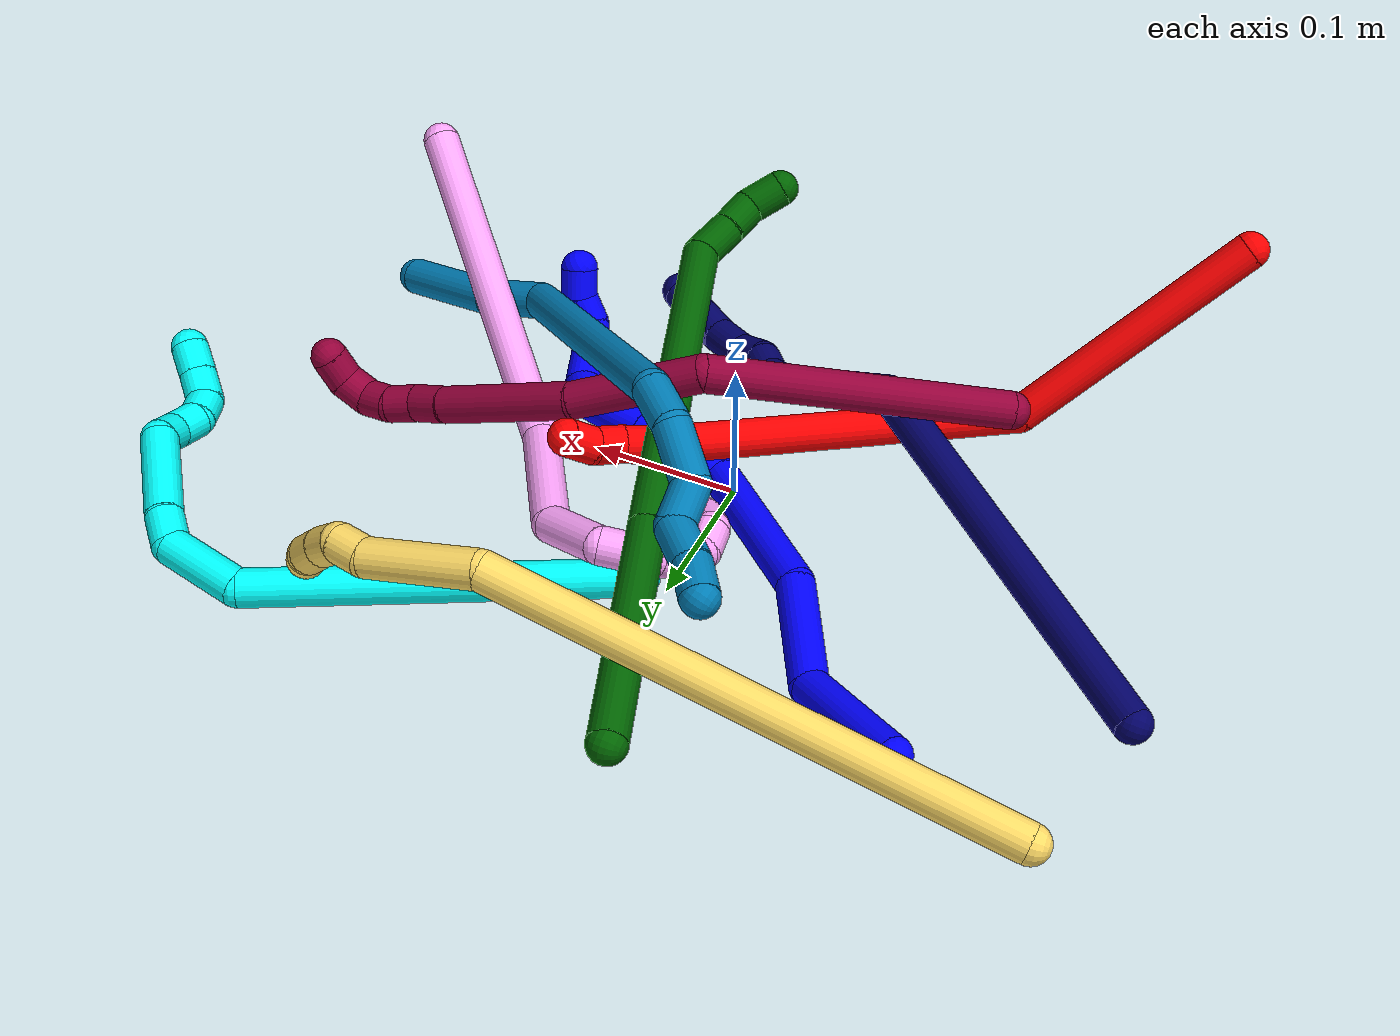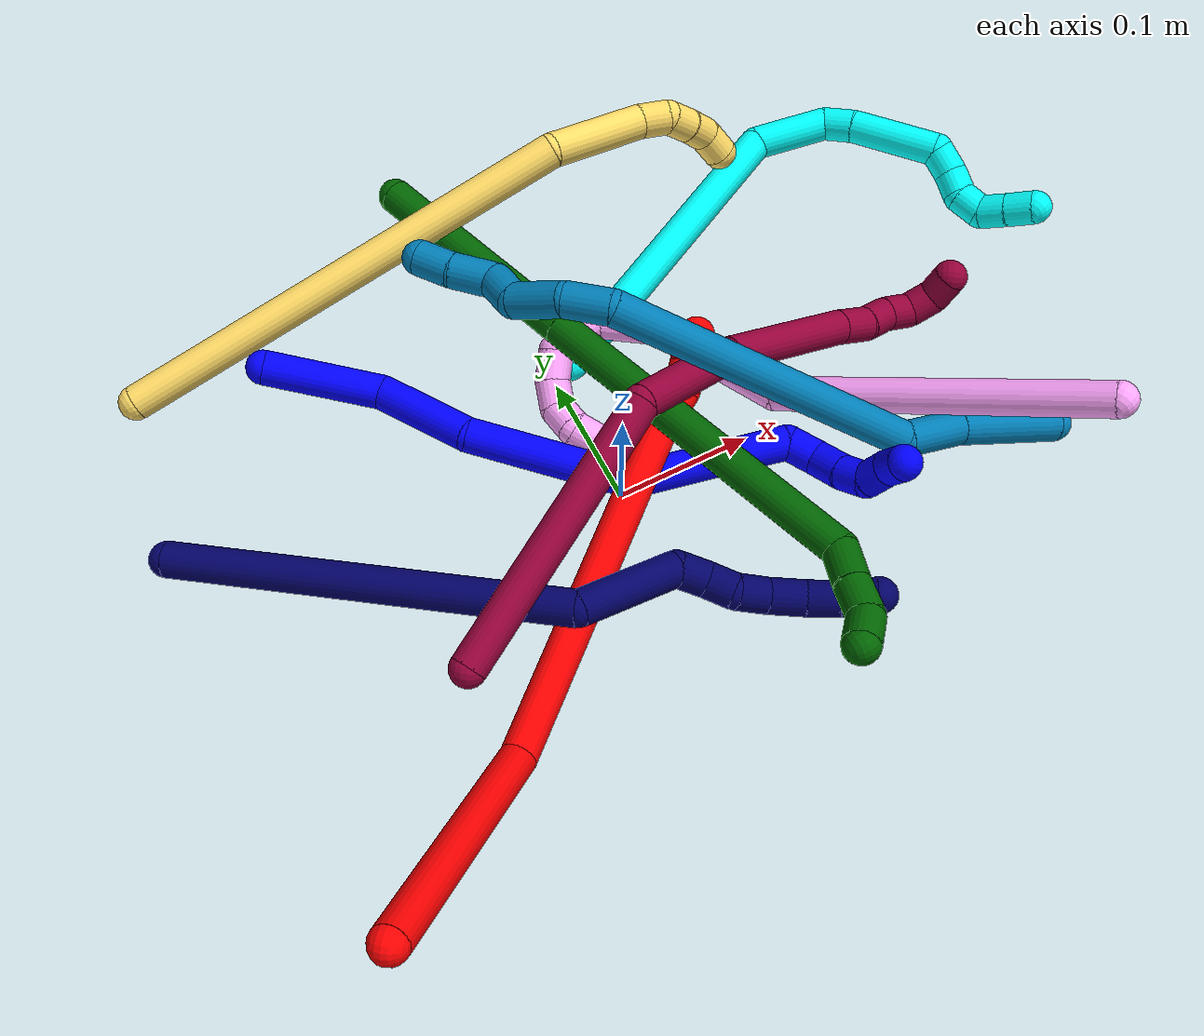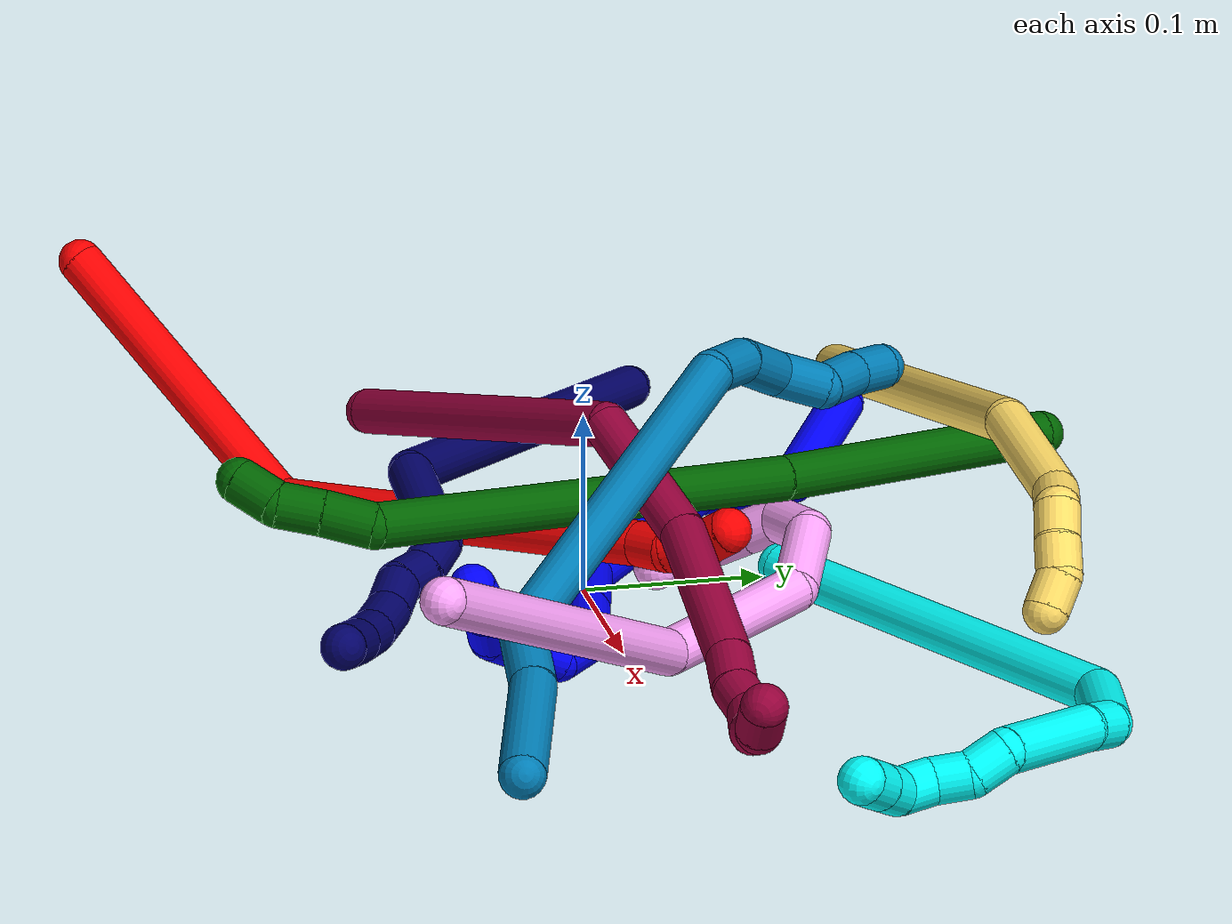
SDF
<sdf version="1.7">
 <world name="default">
  <plugin name="TubeGeneratorPlugin" filename="libtube_generator_plugin.so"/>
  <model name="photoneo_s_sensor">
   <static>1</static>
   <pose>0 0 2 1.57079 1.57079 3.14159</pose>
   <link name="link">
    <inertial><mass>0.1</mass></inertial>
    <sensor name="sensor" type="depth">
     <update_rate>30</update_rate>
     <camera>
      <horizontal_fov>1.22</horizontal_fov>
      <image><width>1920</width><height>1200</height><format>B8G8R8</format></image>
      <clip><near>0.1</near><far>4</far></clip>
      <depth_camera><output>points</output></depth_camera>
     </camera>
     <plugin name="camera_plugin" filename="libgazebo_ros_depth_camera.so">
      <baseline>0.2</baseline>
      <alwaysOn>1</alwaysOn>
      <updateRate>0.0</updateRate>
      <cameraName>camera_ir</cameraName>
      <imageTopicName>/camera/color/image_raw</imageTopicName>
      <cameraInfoTopicName>/camera/color/camera_info</cameraInfoTopicName>
      <depthImageTopicName>/camera/depth/image_raw</depthImageTopicName>
      <depthImageCameraInfoTopicName>/camera/depth/camera_info</depthImageCameraInfoTopicName>
      <pointCloudTopicName>/camera/depth/points</pointCloudTopicName>
      <frameName>fr_optical</frameName>
      <pointCloudCutoff>0.1</pointCloudCutoff>
      <pointCloudCutoffMax>2.0</pointCloudCutoffMax>
      <distortionK1>0</distortionK1>
      <distortionK2>0</distortionK2>
      <distortionK3>0</distortionK3>
      <distortionT1>0</distortionT1>
      <distortionT2>0</distortionT2>
      <CxPrime>0</CxPrime>
      <Cx>0</Cx>
      <Cy>0</Cy>
      <focalLength>0</focalLength>
      <hackBaseline>0</hackBaseline>
     </plugin>
    </sensor>
   </link>
  </model>
  <gravity>0 0 -9.8</gravity>
  <magnetic_field>6e-06 2.3e-05 -4.2e-05</magnetic_field>
  <atmosphere type="adiabatic"/>
  <physics name="default_physics" default="0" type="ode">
   <max_step_size>0.003</max_step_size>
   <real_time_factor>1</real_time_factor>
   <real_time_update_rate>1000</real_time_update_rate>
   <max_contacts>10000</max_contacts>
   <ode>
    <solver>
     <type>quick</type>
     <iters>100</iters>
     <sor>1.3</sor>
     <use_dynamic_moi_rescaling>0</use_dynamic_moi_rescaling>
    </solver>
    <constraints>
     <contact_max_correcting_vel>0</contact_max_correcting_vel>
     <contact_surface_layer>0.001</contact_surface_layer>
     <cfm>0</cfm>
     <erp>0.2</erp>
    </constraints>
   </ode>
  </physics>
  <scene><ambient>0.4 0.4 0.4 1</ambient><background>0.7 0.7 0.7 1</background><shadows>0</shadows></scene>
  <audio><device>default</device></audio>
  <spherical_coordinates>
   <surface_model>EARTH_WGS84</surface_model>
   <latitude_deg>0</latitude_deg>
   <longitude_deg>0</longitude_deg>
   <elevation>0</elevation>
   <heading_deg>0</heading_deg>
  </spherical_coordinates>
  <model name="bin">
   <static>1</static>
   <link name="bottom">
    <collision name="collision-bottom">
     <pose>0 0 -0.01 0 -0 0</pose>
     <geometry><box><size>0.8 0.6 0.02</size></box></geometry>
     <surface>
      <friction><ode><mu>100</mu><mu2>100</mu2></ode></friction>
      <contact><collide_bitmask>65535</collide_bitmask></contact>
     </surface>
    </collision>
   </link>
   <link name="west_wall">
    <collision name="collision-west_wall">
     <pose>-0.41 0 0.1 0 -0 0</pose>
     <geometry><box><size>0.02 0.6 0.2</size></box></geometry>
     <surface>
      <friction><ode><mu>100</mu><mu2>100</mu2></ode></friction>
      <contact><collide_bitmask>65535</collide_bitmask></contact>
     </surface>
    </collision>
   </link>
   <link name="east_wall">
    <collision name="collision-east_wall">
     <pose>0.41 0 0.1 0 -0 0</pose>
     <geometry><box><size>0.02 0.6 0.2</size></box></geometry>
     <surface>
      <friction><ode><mu>100</mu><mu2>100</mu2></ode></friction>
      <contact><collide_bitmask>65535</collide_bitmask></contact>
     </surface>
    </collision>
   </link>
   <link name="south_wall">
    <collision name="collision-south_wall">
     <pose>0 -0.31 0.1 0 -0 0</pose>
     <geometry><box><size>0.8 0.02 0.2</size></box></geometry>
     <surface>
      <friction><ode><mu>100</mu><mu2>100</mu2></ode></friction>
      <contact><collide_bitmask>65535</collide_bitmask></contact>
     </surface>
    </collision>
   </link>
   <link name="north_wall">
    <collision name="collision-north_wall">
     <pose>0 0.31 0.1 0 -0 0</pose>
     <geometry><box><size>0.8 0.02 0.2</size></box></geometry>
     <surface>
      <friction><ode><mu>100</mu><mu2>100</mu2></ode></friction>
      <contact><collide_bitmask>65535</collide_bitmask></contact>
     </surface>
    </collision>
   </link>
  </model>
  <model name="1">
   <static>0</static>
   <link name="1">
    <collision name="collision-cylinder-e_1_1_4">
     <pose>0.019262 -0.02764 0.025845 0.818947 0.470846 0.207463</pose>
     <geometry><cylinder><radius>0.0125</radius><length>0.084923</length></cylinder></geometry>
     <surface>
      <friction><ode><mu>1.16</mu><mu2>1.16</mu2><slip1>0</slip1><slip2>0</slip2></ode></friction>
      <contact><ode><kp>1e+06</kp><kd>1</kd><max_vel>0</max_vel><min_depth>0.001</min_depth></ode></contact>
     </surface>
    </collision>
    <visual name="visual-cylinder-e_1_1_4">
     <pose>0.019262 -0.02764 0.025845 0.818947 0.470846 0.207463</pose>
     <geometry><cylinder><radius>0.0125</radius><length>0.084923</length></cylinder></geometry>
     <material><ambient>0 0 1 1</ambient></material>
    </visual>
    <collision name="collision-cylinder-e_2_4_5">
     <pose>0.063741 -0.08344 0.054414 1.47437 0.728003 0.666046</pose>
     <geometry><cylinder><radius>0.0125</radius><length>0.075797</length></cylinder></geometry>
     <surface>
      <friction><ode><mu>1.16</mu><mu2>1.16</mu2><slip1>0</slip1><slip2>0</slip2></ode></friction>
      <contact><ode><kp>1e+06</kp><kd>1</kd><max_vel>0</max_vel><min_depth>0.001</min_depth></ode></contact>
     </surface>
    </collision>
    <visual name="visual-cylinder-e_2_4_5">
     <pose>0.063741 -0.08344 0.054414 1.47437 0.728003 0.666046</pose>
     <geometry><cylinder><radius>0.0125</radius><length>0.075797</length></cylinder></geometry>
     <material><ambient>0 0 1 1</ambient></material>
    </visual>
    <collision name="collision-cylinder-e_3_5_6">
     <pose>0.120778 -0.154609 0.08231 1.04128 0.568255 0.331826</pose>
     <geometry><cylinder><radius>0.0125</radius><length>0.118253</length></cylinder></geometry>
     <surface>
      <friction><ode><mu>1.16</mu><mu2>1.16</mu2><slip1>0</slip1><slip2>0</slip2></ode></friction>
      <contact><ode><kp>1e+06</kp><kd>1</kd><max_vel>0</max_vel><min_depth>0.001</min_depth></ode></contact>
     </surface>
    </collision>
    <visual name="visual-cylinder-e_3_5_6">
     <pose>0.120778 -0.154609 0.08231 1.04128 0.568255 0.331826</pose>
     <geometry><cylinder><radius>0.0125</radius><length>0.118253</length></cylinder></geometry>
     <material><ambient>0 0 1 1</ambient></material>
    </visual>
    <collision name="collision-cylinder-e_4_6_7">
     <pose>0.15419 -0.225308 0.125951 0.982543 0.047815 0.025585</pose>
     <geometry><cylinder><radius>0.0125</radius><length>0.066644</length></cylinder></geometry>
     <surface>
      <friction><ode><mu>1.16</mu><mu2>1.16</mu2><slip1>0</slip1><slip2>0</slip2></ode></friction>
      <contact><ode><kp>1e+06</kp><kd>1</kd><max_vel>0</max_vel><min_depth>0.001</min_depth></ode></contact>
     </surface>
    </collision>
    <visual name="visual-cylinder-e_4_6_7">
     <pose>0.15419 -0.225308 0.125951 0.982543 0.047815 0.025585</pose>
     <geometry><cylinder><radius>0.0125</radius><length>0.066644</length></cylinder></geometry>
     <material><ambient>0 0 1 1</ambient></material>
    </visual>
    <collision name="collision-cylinder-e_5_7_8">
     <pose>0.1568 -0.271372 0.158174 0.928245 0.044317 0.022187</pose>
     <geometry><cylinder><radius>0.0125</radius><length>0.045948</length></cylinder></geometry>
     <surface>
      <friction><ode><mu>1.16</mu><mu2>1.16</mu2><slip1>0</slip1><slip2>0</slip2></ode></friction>
      <contact><ode><kp>1e+06</kp><kd>1</kd><max_vel>0</max_vel><min_depth>0.001</min_depth></ode></contact>
     </surface>
    </collision>
    <visual name="visual-cylinder-e_5_7_8">
     <pose>0.1568 -0.271372 0.158174 0.928245 0.044317 0.022187</pose>
     <geometry><cylinder><radius>0.0125</radius><length>0.045948</length></cylinder></geometry>
     <material><ambient>0 0 1 1</ambient></material>
    </visual>
    <collision name="collision-cylinder-e_6_8_9">
     <pose>0.165972 -0.296634 0.176099 1.0263 0.791667 0.462538</pose>
     <geometry><cylinder><radius>0.0125</radius><length>0.02292</length></cylinder></geometry>
     <surface>
      <friction><ode><mu>1.16</mu><mu2>1.16</mu2><slip1>0</slip1><slip2>0</slip2></ode></friction>
      <contact><ode><kp>1e+06</kp><kd>1</kd><max_vel>0</max_vel><min_depth>0.001</min_depth></ode></contact>
     </surface>
    </collision>
    <visual name="visual-cylinder-e_6_8_9">
     <pose>0.165972 -0.296634 0.176099 1.0263 0.791667 0.462538</pose>
     <geometry><cylinder><radius>0.0125</radius><length>0.02292</length></cylinder></geometry>
     <material><ambient>0 0 1 1</ambient></material>
    </visual>
    <collision name="collision-cylinder-e_7_9_10">
     <pose>0.181991 -0.312692 0.176398 1.97027 0.668691 0.964905</pose>
     <geometry><cylinder><radius>0.0125</radius><length>0.025372</length></cylinder></geometry>
     <surface>
      <friction><ode><mu>1.16</mu><mu2>1.16</mu2><slip1>0</slip1><slip2>0</slip2></ode></friction>
      <contact><ode><kp>1e+06</kp><kd>1</kd><max_vel>0</max_vel><min_depth>0.001</min_depth></ode></contact>
     </surface>
    </collision>
    <visual name="visual-cylinder-e_7_9_10">
     <pose>0.181991 -0.312692 0.176398 1.97027 0.668691 0.964905</pose>
     <geometry><cylinder><radius>0.0125</radius><length>0.025372</length></cylinder></geometry>
     <material><ambient>0 0 1 1</ambient></material>
    </visual>
    <collision name="collision-cylinder-e_8_10_11">
     <pose>0.195053 -0.330092 0.17007 1.86093 0.544109 0.716536</pose>
     <geometry><cylinder><radius>0.0125</radius><length>0.020078</length></cylinder></geometry>
     <surface>
      <friction><ode><mu>1.16</mu><mu2>1.16</mu2><slip1>0</slip1><slip2>0</slip2></ode></friction>
      <contact><ode><kp>1e+06</kp><kd>1</kd><max_vel>0</max_vel><min_depth>0.001</min_depth></ode></contact>
     </surface>
    </collision>
    <visual name="visual-cylinder-e_8_10_11">
     <pose>0.195053 -0.330092 0.17007 1.86093 0.544109 0.716536</pose>
     <geometry><cylinder><radius>0.0125</radius><length>0.020078</length></cylinder></geometry>
     <material><ambient>0 0 1 1</ambient></material>
    </visual>
    <collision name="collision-cylinder-e_9_11_12">
     <pose>0.198671 -0.347827 0.1649 1.84887 -0.158294 -0.209475</pose>
     <geometry><cylinder><radius>0.0125</radius><length>0.020018</length></cylinder></geometry>
     <surface>
      <friction><ode><mu>1.16</mu><mu2>1.16</mu2><slip1>0</slip1><slip2>0</slip2></ode></friction>
      <contact><ode><kp>1e+06</kp><kd>1</kd><max_vel>0</max_vel><min_depth>0.001</min_depth></ode></contact>
     </surface>
    </collision>
    <visual name="visual-cylinder-e_9_11_12">
     <pose>0.198671 -0.347827 0.1649 1.84887 -0.158294 -0.209475</pose>
     <geometry><cylinder><radius>0.0125</radius><length>0.020018</length></cylinder></geometry>
     <material><ambient>0 0 1 1</ambient></material>
    </visual>
    <collision name="collision-cylinder-e_10_12_2">
     <pose>0.197453 -0.365311 0.156131 2.21991 0.035895 0.072273</pose>
     <geometry><cylinder><radius>0.0125</radius><length>0.020047</length></cylinder></geometry>
     <surface>
      <friction><ode><mu>1.16</mu><mu2>1.16</mu2><slip1>0</slip1><slip2>0</slip2></ode></friction>
      <contact><ode><kp>1e+06</kp><kd>1</kd><max_vel>0</max_vel><min_depth>0.001</min_depth></ode></contact>
     </surface>
    </collision>
    <visual name="visual-cylinder-e_10_12_2">
     <pose>0.197453 -0.365311 0.156131 2.21991 0.035895 0.072273</pose>
     <geometry><cylinder><radius>0.0125</radius><length>0.020047</length></cylinder></geometry>
     <material><ambient>0 0 1 1</ambient></material>
    </visual>
    <collision name="collision-sphere-2">
     <pose>0.197813 -0.373291 0.150076 0 -0 0</pose>
     <geometry><sphere><radius>0.0125</radius></sphere></geometry>
     <surface>
      <friction><ode><mu>1.16</mu><mu2>1.16</mu2><slip1>0</slip1><slip2>0</slip2></ode></friction>
      <contact><ode><kp>1e+06</kp><kd>1</kd><max_vel>0</max_vel><min_depth>0.001</min_depth></ode></contact>
     </surface>
    </collision>
    <visual name="visual-sphere-2">
     <pose>0.197813 -0.373291 0.150076 0 -0 0</pose>
     <geometry><sphere><radius>0.0125</radius></sphere></geometry>
     <material><ambient>0 0 1 1</ambient></material>
    </visual>
    <collision name="collision-sphere-12">
     <pose>0.197094 -0.357331 0.162186 0 -0 0</pose>
     <geometry><sphere><radius>0.0125</radius></sphere></geometry>
     <surface>
      <friction><ode><mu>1.16</mu><mu2>1.16</mu2><slip1>0</slip1><slip2>0</slip2></ode></friction>
      <contact><ode><kp>1e+06</kp><kd>1</kd><max_vel>0</max_vel><min_depth>0.001</min_depth></ode></contact>
     </surface>
    </collision>
    <visual name="visual-sphere-12">
     <pose>0.197094 -0.357331 0.162186 0 -0 0</pose>
     <geometry><sphere><radius>0.0125</radius></sphere></geometry>
     <material><ambient>0 0 1 1</ambient></material>
    </visual>
    <collision name="collision-sphere-11">
     <pose>0.200249 -0.338323 0.167613 0 -0 0</pose>
     <geometry><sphere><radius>0.0125</radius></sphere></geometry>
     <surface>
      <friction><ode><mu>1.16</mu><mu2>1.16</mu2><slip1>0</slip1><slip2>0</slip2></ode></friction>
      <contact><ode><kp>1e+06</kp><kd>1</kd><max_vel>0</max_vel><min_depth>0.001</min_depth></ode></contact>
     </surface>
    </collision>
    <visual name="visual-sphere-11">
     <pose>0.200249 -0.338323 0.167613 0 -0 0</pose>
     <geometry><sphere><radius>0.0125</radius></sphere></geometry>
     <material><ambient>0 0 1 1</ambient></material>
    </visual>
    <collision name="collision-sphere-10">
     <pose>0.189856 -0.321862 0.172527 0 -0 0</pose>
     <geometry><sphere><radius>0.0125</radius></sphere></geometry>
     <surface>
      <friction><ode><mu>1.16</mu><mu2>1.16</mu2><slip1>0</slip1><slip2>0</slip2></ode></friction>
      <contact><ode><kp>1e+06</kp><kd>1</kd><max_vel>0</max_vel><min_depth>0.001</min_depth></ode></contact>
     </surface>
    </collision>
    <visual name="visual-sphere-10">
     <pose>0.189856 -0.321862 0.172527 0 -0 0</pose>
     <geometry><sphere><radius>0.0125</radius></sphere></geometry>
     <material><ambient>0 0 1 1</ambient></material>
    </visual>
    <collision name="collision-sphere-9">
     <pose>0.174126 -0.303522 0.18027 0 -0 0</pose>
     <geometry><sphere><radius>0.0125</radius></sphere></geometry>
     <surface>
      <friction><ode><mu>1.16</mu><mu2>1.16</mu2><slip1>0</slip1><slip2>0</slip2></ode></friction>
      <contact><ode><kp>1e+06</kp><kd>1</kd><max_vel>0</max_vel><min_depth>0.001</min_depth></ode></contact>
     </surface>
    </collision>
    <visual name="visual-sphere-9">
     <pose>0.174126 -0.303522 0.18027 0 -0 0</pose>
     <geometry><sphere><radius>0.0125</radius></sphere></geometry>
     <material><ambient>0 0 1 1</ambient></material>
    </visual>
    <collision name="collision-sphere-4">
     <pose>0.038524 -0.05528 0.05169 0 -0 0</pose>
     <geometry><sphere><radius>0.0125</radius></sphere></geometry>
     <surface>
      <friction><ode><mu>1.16</mu><mu2>1.16</mu2><slip1>0</slip1><slip2>0</slip2></ode></friction>
      <contact><ode><kp>1e+06</kp><kd>1</kd><max_vel>0</max_vel><min_depth>0.001</min_depth></ode></contact>
     </surface>
    </collision>
    <visual name="visual-sphere-4">
     <pose>0.038524 -0.05528 0.05169 0 -0 0</pose>
     <geometry><sphere><radius>0.0125</radius></sphere></geometry>
     <material><ambient>0 0 1 1</ambient></material>
    </visual>
    <collision name="collision-sphere-1">
     <geometry><sphere><radius>0.0125</radius></sphere></geometry>
     <surface>
      <friction><ode><mu>1.16</mu><mu2>1.16</mu2><slip1>0</slip1><slip2>0</slip2></ode></friction>
      <contact><ode><kp>1e+06</kp><kd>1</kd><max_vel>0</max_vel><min_depth>0.001</min_depth></ode></contact>
     </surface>
    </collision>
    <visual name="visual-sphere-1">
     <geometry><sphere><radius>0.0125</radius></sphere></geometry>
     <material><ambient>0 0 1 1</ambient></material>
    </visual>
    <collision name="collision-sphere-8">
     <pose>0.157818 -0.289746 0.171928 0 -0 0</pose>
     <geometry><sphere><radius>0.0125</radius></sphere></geometry>
     <surface>
      <friction><ode><mu>1.16</mu><mu2>1.16</mu2><slip1>0</slip1><slip2>0</slip2></ode></friction>
      <contact><ode><kp>1e+06</kp><kd>1</kd><max_vel>0</max_vel><min_depth>0.001</min_depth></ode></contact>
     </surface>
    </collision>
    <visual name="visual-sphere-8">
     <pose>0.157818 -0.289746 0.171928 0 -0 0</pose>
     <geometry><sphere><radius>0.0125</radius></sphere></geometry>
     <material><ambient>0 0 1 1</ambient></material>
    </visual>
    <collision name="collision-sphere-5">
     <pose>0.088958 -0.1116 0.057138 0 -0 0</pose>
     <geometry><sphere><radius>0.0125</radius></sphere></geometry>
     <surface>
      <friction><ode><mu>1.16</mu><mu2>1.16</mu2><slip1>0</slip1><slip2>0</slip2></ode></friction>
      <contact><ode><kp>1e+06</kp><kd>1</kd><max_vel>0</max_vel><min_depth>0.001</min_depth></ode></contact>
     </surface>
    </collision>
    <visual name="visual-sphere-5">
     <pose>0.088958 -0.1116 0.057138 0 -0 0</pose>
     <geometry><sphere><radius>0.0125</radius></sphere></geometry>
     <material><ambient>0 0 1 1</ambient></material>
    </visual>
    <collision name="collision-sphere-6">
     <pose>0.152597 -0.197619 0.107482 0 -0 0</pose>
     <geometry><sphere><radius>0.0125</radius></sphere></geometry>
     <surface>
      <friction><ode><mu>1.16</mu><mu2>1.16</mu2><slip1>0</slip1><slip2>0</slip2></ode></friction>
      <contact><ode><kp>1e+06</kp><kd>1</kd><max_vel>0</max_vel><min_depth>0.001</min_depth></ode></contact>
     </surface>
    </collision>
    <visual name="visual-sphere-6">
     <pose>0.152597 -0.197619 0.107482 0 -0 0</pose>
     <geometry><sphere><radius>0.0125</radius></sphere></geometry>
     <material><ambient>0 0 1 1</ambient></material>
    </visual>
    <collision name="collision-sphere-7">
     <pose>0.155782 -0.252997 0.144421 0 -0 0</pose>
     <geometry><sphere><radius>0.0125</radius></sphere></geometry>
     <surface>
      <friction><ode><mu>1.16</mu><mu2>1.16</mu2><slip1>0</slip1><slip2>0</slip2></ode></friction>
      <contact><ode><kp>1e+06</kp><kd>1</kd><max_vel>0</max_vel><min_depth>0.001</min_depth></ode></contact>
     </surface>
    </collision>
    <visual name="visual-sphere-7">
     <pose>0.155782 -0.252997 0.144421 0 -0 0</pose>
     <geometry><sphere><radius>0.0125</radius></sphere></geometry>
     <material><ambient>0 0 1 1</ambient></material>
    </visual>
    <inertial>
     <pose>0.117007 -0.180171 0.100143 0 -0 0</pose>
     <mass>0.5</mass>
     <inertia>
      <ixx>0.000313</ixx>
      <ixy>0</ixy>
      <ixz>0</ixz>
      <iyy>0.000212</iyy>
      <iyz>0</iyz>
      <izz>8.4e-05</izz>
     </inertia>
    </inertial>
   </link>
   <pose>-0.184834 0.191086 0.032102 -2.47096 0.374016 -1.73083</pose>
  </model>
  <model name="2">
   <static>0</static>
   <link name="2">
    <collision name="collision-cylinder-e_1_1_4">
     <pose>0.084828 -0.034982 0.005211 1.42292 1.17578 1.04302</pose>
     <geometry><cylinder><radius>0.0125</radius><length>0.183811</length></cylinder></geometry>
     <surface>
      <friction><ode><mu>1.16</mu><mu2>1.16</mu2><slip1>0</slip1><slip2>0</slip2></ode></friction>
      <contact><ode><kp>1e+06</kp><kd>1</kd><max_vel>0</max_vel><min_depth>0.001</min_depth></ode></contact>
     </surface>
    </collision>
    <visual name="visual-cylinder-e_1_1_4">
     <pose>0.084828 -0.034982 0.005211 1.42292 1.17578 1.04302</pose>
     <geometry><cylinder><radius>0.0125</radius><length>0.183811</length></cylinder></geometry>
     <material><ambient>1 0 0 1</ambient></material>
    </visual>
    <collision name="collision-cylinder-e_2_4_5">
     <pose>0.285411 -0.02598 0.034184 -1.07547 1.16312 -0.747261</pose>
     <geometry><cylinder><radius>0.0125</radius><length>0.252179</length></cylinder></geometry>
     <surface>
      <friction><ode><mu>1.16</mu><mu2>1.16</mu2><slip1>0</slip1><slip2>0</slip2></ode></friction>
      <contact><ode><kp>1e+06</kp><kd>1</kd><max_vel>0</max_vel><min_depth>0.001</min_depth></ode></contact>
     </surface>
    </collision>
    <visual name="visual-cylinder-e_2_4_5">
     <pose>0.285411 -0.02598 0.034184 -1.07547 1.16312 -0.747261</pose>
     <geometry><cylinder><radius>0.0125</radius><length>0.252179</length></cylinder></geometry>
     <material><ambient>1 0 0 1</ambient></material>
    </visual>
    <collision name="collision-cylinder-e_3_5_6">
     <pose>0.411002 0.021438 0.061988 -0.704292 1.07614 -0.431776</pose>
     <geometry><cylinder><radius>0.0125</radius><length>0.022348</length></cylinder></geometry>
     <surface>
      <friction><ode><mu>1.16</mu><mu2>1.16</mu2><slip1>0</slip1><slip2>0</slip2></ode></friction>
      <contact><ode><kp>1e+06</kp><kd>1</kd><max_vel>0</max_vel><min_depth>0.001</min_depth></ode></contact>
     </surface>
    </collision>
    <visual name="visual-cylinder-e_3_5_6">
     <pose>0.411002 0.021438 0.061988 -0.704292 1.07614 -0.431776</pose>
     <geometry><cylinder><radius>0.0125</radius><length>0.022348</length></cylinder></geometry>
     <material><ambient>1 0 0 1</ambient></material>
    </visual>
    <collision name="collision-cylinder-e_4_6_7">
     <pose>0.429712 0.030582 0.066377 -1.51021 0.998336 -0.948228</pose>
     <geometry><cylinder><radius>0.0125</radius><length>0.021117</length></cylinder></geometry>
     <surface>
      <friction><ode><mu>1.16</mu><mu2>1.16</mu2><slip1>0</slip1><slip2>0</slip2></ode></friction>
      <contact><ode><kp>1e+06</kp><kd>1</kd><max_vel>0</max_vel><min_depth>0.001</min_depth></ode></contact>
     </surface>
    </collision>
    <visual name="visual-cylinder-e_4_6_7">
     <pose>0.429712 0.030582 0.066377 -1.51021 0.998336 -0.948228</pose>
     <geometry><cylinder><radius>0.0125</radius><length>0.021117</length></cylinder></geometry>
     <material><ambient>1 0 0 1</ambient></material>
    </visual>
    <collision name="collision-cylinder-e_5_7_2">
     <pose>0.445244 0.043821 0.068843 -1.29643 0.705091 -0.543525</pose>
     <geometry><cylinder><radius>0.0125</radius><length>0.020545</length></cylinder></geometry>
     <surface>
      <friction><ode><mu>1.16</mu><mu2>1.16</mu2><slip1>0</slip1><slip2>0</slip2></ode></friction>
      <contact><ode><kp>1e+06</kp><kd>1</kd><max_vel>0</max_vel><min_depth>0.001</min_depth></ode></contact>
     </surface>
    </collision>
    <visual name="visual-cylinder-e_5_7_2">
     <pose>0.445244 0.043821 0.068843 -1.29643 0.705091 -0.543525</pose>
     <geometry><cylinder><radius>0.0125</radius><length>0.020545</length></cylinder></geometry>
     <material><ambient>1 0 0 1</ambient></material>
    </visual>
    <collision name="collision-sphere-2">
     <pose>0.451902 0.051351 0.070962 0 -0 0</pose>
     <geometry><sphere><radius>0.0125</radius></sphere></geometry>
     <surface>
      <friction><ode><mu>1.16</mu><mu2>1.16</mu2><slip1>0</slip1><slip2>0</slip2></ode></friction>
      <contact><ode><kp>1e+06</kp><kd>1</kd><max_vel>0</max_vel><min_depth>0.001</min_depth></ode></contact>
     </surface>
    </collision>
    <visual name="visual-sphere-2">
     <pose>0.451902 0.051351 0.070962 0 -0 0</pose>
     <geometry><sphere><radius>0.0125</radius></sphere></geometry>
     <material><ambient>1 0 0 1</ambient></material>
    </visual>
    <collision name="collision-sphere-7">
     <pose>0.438587 0.036291 0.066723 0 -0 0</pose>
     <geometry><sphere><radius>0.0125</radius></sphere></geometry>
     <surface>
      <friction><ode><mu>1.16</mu><mu2>1.16</mu2><slip1>0</slip1><slip2>0</slip2></ode></friction>
      <contact><ode><kp>1e+06</kp><kd>1</kd><max_vel>0</max_vel><min_depth>0.001</min_depth></ode></contact>
     </surface>
    </collision>
    <visual name="visual-sphere-7">
     <pose>0.438587 0.036291 0.066723 0 -0 0</pose>
     <geometry><sphere><radius>0.0125</radius></sphere></geometry>
     <material><ambient>1 0 0 1</ambient></material>
    </visual>
    <collision name="collision-sphere-6">
     <pose>0.420837 0.024872 0.066031 0 -0 0</pose>
     <geometry><sphere><radius>0.0125</radius></sphere></geometry>
     <surface>
      <friction><ode><mu>1.16</mu><mu2>1.16</mu2><slip1>0</slip1><slip2>0</slip2></ode></friction>
      <contact><ode><kp>1e+06</kp><kd>1</kd><max_vel>0</max_vel><min_depth>0.001</min_depth></ode></contact>
     </surface>
    </collision>
    <visual name="visual-sphere-6">
     <pose>0.420837 0.024872 0.066031 0 -0 0</pose>
     <geometry><sphere><radius>0.0125</radius></sphere></geometry>
     <material><ambient>1 0 0 1</ambient></material>
    </visual>
    <collision name="collision-sphere-5">
     <pose>0.401167 0.018003 0.057946 0 -0 0</pose>
     <geometry><sphere><radius>0.0125</radius></sphere></geometry>
     <surface>
      <friction><ode><mu>1.16</mu><mu2>1.16</mu2><slip1>0</slip1><slip2>0</slip2></ode></friction>
      <contact><ode><kp>1e+06</kp><kd>1</kd><max_vel>0</max_vel><min_depth>0.001</min_depth></ode></contact>
     </surface>
    </collision>
    <visual name="visual-sphere-5">
     <pose>0.401167 0.018003 0.057946 0 -0 0</pose>
     <geometry><sphere><radius>0.0125</radius></sphere></geometry>
     <material><ambient>1 0 0 1</ambient></material>
    </visual>
    <collision name="collision-sphere-1">
     <geometry><sphere><radius>0.0125</radius></sphere></geometry>
     <surface>
      <friction><ode><mu>1.16</mu><mu2>1.16</mu2><slip1>0</slip1><slip2>0</slip2></ode></friction>
      <contact><ode><kp>1e+06</kp><kd>1</kd><max_vel>0</max_vel><min_depth>0.001</min_depth></ode></contact>
     </surface>
    </collision>
    <visual name="visual-sphere-1">
     <geometry><sphere><radius>0.0125</radius></sphere></geometry>
     <material><ambient>1 0 0 1</ambient></material>
    </visual>
    <collision name="collision-sphere-4">
     <pose>0.169655 -0.069963 0.010422 0 -0 0</pose>
     <geometry><sphere><radius>0.0125</radius></sphere></geometry>
     <surface>
      <friction><ode><mu>1.16</mu><mu2>1.16</mu2><slip1>0</slip1><slip2>0</slip2></ode></friction>
      <contact><ode><kp>1e+06</kp><kd>1</kd><max_vel>0</max_vel><min_depth>0.001</min_depth></ode></contact>
     </surface>
    </collision>
    <visual name="visual-sphere-4">
     <pose>0.169655 -0.069963 0.010422 0 -0 0</pose>
     <geometry><sphere><radius>0.0125</radius></sphere></geometry>
     <material><ambient>1 0 0 1</ambient></material>
    </visual>
    <inertial>
     <pose>0.229948 -0.021913 0.027559 0 -0 0</pose>
     <mass>0.5</mass>
     <inertia>
      <ixx>0.000341</ixx>
      <ixy>0</ixy>
      <ixz>0</ixz>
      <iyy>0.001479</iyy>
      <iyz>0</iyz>
      <izz>-0.001991</izz>
     </inertia>
    </inertial>
   </link>
   <pose>-0.260076 -0.233716 0.122152 1.40958 0.270618 0.833934</pose>
  </model>
  <model name="3">
   <static>0</static>
   <link name="3">
    <collision name="collision-cylinder-e_1_1_4">
     <pose>-0.002709 -0.001757 0.124394 0.01412 -0.021776 -0.000154</pose>
     <geometry><cylinder><radius>0.0125</radius><length>0.248871</length></cylinder></geometry>
     <surface>
      <friction><ode><mu>1.16</mu><mu2>1.16</mu2><slip1>0</slip1><slip2>0</slip2></ode></friction>
      <contact><ode><kp>1e+06</kp><kd>1</kd><max_vel>0</max_vel><min_depth>0.001</min_depth></ode></contact>
     </surface>
    </collision>
    <visual name="visual-cylinder-e_1_1_4">
     <pose>-0.002709 -0.001757 0.124394 0.01412 -0.021776 -0.000154</pose>
     <geometry><cylinder><radius>0.0125</radius><length>0.248871</length></cylinder></geometry>
     <material><ambient>0.003922 1 0.996078 1</ambient></material>
    </visual>
    <collision name="collision-cylinder-e_2_4_5">
     <pose>0.011413 -0.007184 0.27141 0.160852 0.633455 0.052823</pose>
     <geometry><cylinder><radius>0.0125</radius><length>0.056871</length></cylinder></geometry>
     <surface>
      <friction><ode><mu>1.16</mu><mu2>1.16</mu2><slip1>0</slip1><slip2>0</slip2></ode></friction>
      <contact><ode><kp>1e+06</kp><kd>1</kd><max_vel>0</max_vel><min_depth>0.001</min_depth></ode></contact>
     </surface>
    </collision>
    <visual name="visual-cylinder-e_2_4_5">
     <pose>0.011413 -0.007184 0.27141 0.160852 0.633455 0.052823</pose>
     <geometry><cylinder><radius>0.0125</radius><length>0.056871</length></cylinder></geometry>
     <material><ambient>0.003922 1 0.996078 1</ambient></material>
    </visual>
    <collision name="collision-cylinder-e_3_5_6">
     <pose>0.038957 -0.014474 0.29745 0.814134 1.13578 0.536866</pose>
     <geometry><cylinder><radius>0.0125</radius><length>0.023625</length></cylinder></geometry>
     <surface>
      <friction><ode><mu>1.16</mu><mu2>1.16</mu2><slip1>0</slip1><slip2>0</slip2></ode></friction>
      <contact><ode><kp>1e+06</kp><kd>1</kd><max_vel>0</max_vel><min_depth>0.001</min_depth></ode></contact>
     </surface>
    </collision>
    <visual name="visual-cylinder-e_3_5_6">
     <pose>0.038957 -0.014474 0.29745 0.814134 1.13578 0.536866</pose>
     <geometry><cylinder><radius>0.0125</radius><length>0.023625</length></cylinder></geometry>
     <material><ambient>0.003922 1 0.996078 1</ambient></material>
    </visual>
    <collision name="collision-cylinder-e_4_6_7">
     <pose>0.082189 -0.024455 0.306772 0.822587 1.31 0.64656</pose>
     <geometry><cylinder><radius>0.0125</radius><length>0.067315</length></cylinder></geometry>
     <surface>
      <friction><ode><mu>1.16</mu><mu2>1.16</mu2><slip1>0</slip1><slip2>0</slip2></ode></friction>
      <contact><ode><kp>1e+06</kp><kd>1</kd><max_vel>0</max_vel><min_depth>0.001</min_depth></ode></contact>
     </surface>
    </collision>
    <visual name="visual-cylinder-e_4_6_7">
     <pose>0.082189 -0.024455 0.306772 0.822587 1.31 0.64656</pose>
     <geometry><cylinder><radius>0.0125</radius><length>0.067315</length></cylinder></geometry>
     <material><ambient>0.003922 1 0.996078 1</ambient></material>
    </visual>
    <collision name="collision-cylinder-e_5_7_8">
     <pose>0.124056 -0.026591 0.310073 -2.12315 1.08277 -1.64488</pose>
     <geometry><cylinder><radius>0.0125</radius><length>0.021165</length></cylinder></geometry>
     <surface>
      <friction><ode><mu>1.16</mu><mu2>1.16</mu2><slip1>0</slip1><slip2>0</slip2></ode></friction>
      <contact><ode><kp>1e+06</kp><kd>1</kd><max_vel>0</max_vel><min_depth>0.001</min_depth></ode></contact>
     </surface>
    </collision>
    <visual name="visual-cylinder-e_5_7_8">
     <pose>0.124056 -0.026591 0.310073 -2.12315 1.08277 -1.64488</pose>
     <geometry><cylinder><radius>0.0125</radius><length>0.021165</length></cylinder></geometry>
     <material><ambient>0.003922 1 0.996078 1</ambient></material>
    </visual>
    <collision name="collision-cylinder-e_6_8_9">
     <pose>0.141541 -0.021252 0.301436 -2.9589 0.924788 -2.77809</pose>
     <geometry><cylinder><radius>0.0125</radius><length>0.020384</length></cylinder></geometry>
     <surface>
      <friction><ode><mu>1.16</mu><mu2>1.16</mu2><slip1>0</slip1><slip2>0</slip2></ode></friction>
      <contact><ode><kp>1e+06</kp><kd>1</kd><max_vel>0</max_vel><min_depth>0.001</min_depth></ode></contact>
     </surface>
    </collision>
    <visual name="visual-cylinder-e_6_8_9">
     <pose>0.141541 -0.021252 0.301436 -2.9589 0.924788 -2.77809</pose>
     <geometry><cylinder><radius>0.0125</radius><length>0.020384</length></cylinder></geometry>
     <material><ambient>0.003922 1 0.996078 1</ambient></material>
    </visual>
    <collision name="collision-cylinder-e_7_9_10">
     <pose>0.159754 -0.020135 0.294085 -3.13966 1.44077 -3.13939</pose>
     <geometry><cylinder><radius>0.0125</radius><length>0.020322</length></cylinder></geometry>
     <surface>
      <friction><ode><mu>1.16</mu><mu2>1.16</mu2><slip1>0</slip1><slip2>0</slip2></ode></friction>
      <contact><ode><kp>1e+06</kp><kd>1</kd><max_vel>0</max_vel><min_depth>0.001</min_depth></ode></contact>
     </surface>
    </collision>
    <visual name="visual-cylinder-e_7_9_10">
     <pose>0.159754 -0.020135 0.294085 -3.13966 1.44077 -3.13939</pose>
     <geometry><cylinder><radius>0.0125</radius><length>0.020322</length></cylinder></geometry>
     <material><ambient>0.003922 1 0.996078 1</ambient></material>
    </visual>
    <collision name="collision-cylinder-e_8_10_11">
     <pose>0.178059 -0.025444 0.295762 1.05746 0.933065 0.572283</pose>
     <geometry><cylinder><radius>0.0125</radius><length>0.020485</length></cylinder></geometry>
     <surface>
      <friction><ode><mu>1.16</mu><mu2>1.16</mu2><slip1>0</slip1><slip2>0</slip2></ode></friction>
      <contact><ode><kp>1e+06</kp><kd>1</kd><max_vel>0</max_vel><min_depth>0.001</min_depth></ode></contact>
     </surface>
    </collision>
    <visual name="visual-cylinder-e_8_10_11">
     <pose>0.178059 -0.025444 0.295762 1.05746 0.933065 0.572283</pose>
     <geometry><cylinder><radius>0.0125</radius><length>0.020485</length></cylinder></geometry>
     <material><ambient>0.003922 1 0.996078 1</ambient></material>
    </visual>
    <collision name="collision-cylinder-e_9_11_2">
     <pose>0.194563 -0.036277 0.302059 1.0316 0.909987 0.541178</pose>
     <geometry><cylinder><radius>0.0125</radius><length>0.020961</length></cylinder></geometry>
     <surface>
      <friction><ode><mu>1.16</mu><mu2>1.16</mu2><slip1>0</slip1><slip2>0</slip2></ode></friction>
      <contact><ode><kp>1e+06</kp><kd>1</kd><max_vel>0</max_vel><min_depth>0.001</min_depth></ode></contact>
     </surface>
    </collision>
    <visual name="visual-cylinder-e_9_11_2">
     <pose>0.194563 -0.036277 0.302059 1.0316 0.909987 0.541178</pose>
     <geometry><cylinder><radius>0.0125</radius><length>0.020961</length></cylinder></geometry>
     <material><ambient>0.003922 1 0.996078 1</ambient></material>
    </visual>
    <collision name="collision-sphere-2">
     <pose>0.202838 -0.041797 0.305362 0 -0 0</pose>
     <geometry><sphere><radius>0.0125</radius></sphere></geometry>
     <surface>
      <friction><ode><mu>1.16</mu><mu2>1.16</mu2><slip1>0</slip1><slip2>0</slip2></ode></friction>
      <contact><ode><kp>1e+06</kp><kd>1</kd><max_vel>0</max_vel><min_depth>0.001</min_depth></ode></contact>
     </surface>
    </collision>
    <visual name="visual-sphere-2">
     <pose>0.202838 -0.041797 0.305362 0 -0 0</pose>
     <geometry><sphere><radius>0.0125</radius></sphere></geometry>
     <material><ambient>0.003922 1 0.996078 1</ambient></material>
    </visual>
    <collision name="collision-sphere-11">
     <pose>0.186289 -0.030757 0.298757 0 -0 0</pose>
     <geometry><sphere><radius>0.0125</radius></sphere></geometry>
     <surface>
      <friction><ode><mu>1.16</mu><mu2>1.16</mu2><slip1>0</slip1><slip2>0</slip2></ode></friction>
      <contact><ode><kp>1e+06</kp><kd>1</kd><max_vel>0</max_vel><min_depth>0.001</min_depth></ode></contact>
     </surface>
    </collision>
    <visual name="visual-sphere-11">
     <pose>0.186289 -0.030757 0.298757 0 -0 0</pose>
     <geometry><sphere><radius>0.0125</radius></sphere></geometry>
     <material><ambient>0.003922 1 0.996078 1</ambient></material>
    </visual>
    <collision name="collision-sphere-10">
     <pose>0.16983 -0.020132 0.292767 0 -0 0</pose>
     <geometry><sphere><radius>0.0125</radius></sphere></geometry>
     <surface>
      <friction><ode><mu>1.16</mu><mu2>1.16</mu2><slip1>0</slip1><slip2>0</slip2></ode></friction>
      <contact><ode><kp>1e+06</kp><kd>1</kd><max_vel>0</max_vel><min_depth>0.001</min_depth></ode></contact>
     </surface>
    </collision>
    <visual name="visual-sphere-10">
     <pose>0.16983 -0.020132 0.292767 0 -0 0</pose>
     <geometry><sphere><radius>0.0125</radius></sphere></geometry>
     <material><ambient>0.003922 1 0.996078 1</ambient></material>
    </visual>
    <collision name="collision-sphere-9">
     <pose>0.149679 -0.020137 0.295402 0 -0 0</pose>
     <geometry><sphere><radius>0.0125</radius></sphere></geometry>
     <surface>
      <friction><ode><mu>1.16</mu><mu2>1.16</mu2><slip1>0</slip1><slip2>0</slip2></ode></friction>
      <contact><ode><kp>1e+06</kp><kd>1</kd><max_vel>0</max_vel><min_depth>0.001</min_depth></ode></contact>
     </surface>
    </collision>
    <visual name="visual-sphere-9">
     <pose>0.149679 -0.020137 0.295402 0 -0 0</pose>
     <geometry><sphere><radius>0.0125</radius></sphere></geometry>
     <material><ambient>0.003922 1 0.996078 1</ambient></material>
    </visual>
    <collision name="collision-sphere-4">
     <pose>-0.005419 -0.003513 0.248787 0 -0 0</pose>
     <geometry><sphere><radius>0.0125</radius></sphere></geometry>
     <surface>
      <friction><ode><mu>1.16</mu><mu2>1.16</mu2><slip1>0</slip1><slip2>0</slip2></ode></friction>
      <contact><ode><kp>1e+06</kp><kd>1</kd><max_vel>0</max_vel><min_depth>0.001</min_depth></ode></contact>
     </surface>
    </collision>
    <visual name="visual-sphere-4">
     <pose>-0.005419 -0.003513 0.248787 0 -0 0</pose>
     <geometry><sphere><radius>0.0125</radius></sphere></geometry>
     <material><ambient>0.003922 1 0.996078 1</ambient></material>
    </visual>
    <collision name="collision-sphere-1">
     <geometry><sphere><radius>0.0125</radius></sphere></geometry>
     <surface>
      <friction><ode><mu>1.16</mu><mu2>1.16</mu2><slip1>0</slip1><slip2>0</slip2></ode></friction>
      <contact><ode><kp>1e+06</kp><kd>1</kd><max_vel>0</max_vel><min_depth>0.001</min_depth></ode></contact>
     </surface>
    </collision>
    <visual name="visual-sphere-1">
     <geometry><sphere><radius>0.0125</radius></sphere></geometry>
     <material><ambient>0.003922 1 0.996078 1</ambient></material>
    </visual>
    <collision name="collision-sphere-8">
     <pose>0.133403 -0.022367 0.307469 0 -0 0</pose>
     <geometry><sphere><radius>0.0125</radius></sphere></geometry>
     <surface>
      <friction><ode><mu>1.16</mu><mu2>1.16</mu2><slip1>0</slip1><slip2>0</slip2></ode></friction>
      <contact><ode><kp>1e+06</kp><kd>1</kd><max_vel>0</max_vel><min_depth>0.001</min_depth></ode></contact>
     </surface>
    </collision>
    <visual name="visual-sphere-8">
     <pose>0.133403 -0.022367 0.307469 0 -0 0</pose>
     <geometry><sphere><radius>0.0125</radius></sphere></geometry>
     <material><ambient>0.003922 1 0.996078 1</ambient></material>
    </visual>
    <collision name="collision-sphere-5">
     <pose>0.028245 -0.010854 0.294033 0 -0 0</pose>
     <geometry><sphere><radius>0.0125</radius></sphere></geometry>
     <surface>
      <friction><ode><mu>1.16</mu><mu2>1.16</mu2><slip1>0</slip1><slip2>0</slip2></ode></friction>
      <contact><ode><kp>1e+06</kp><kd>1</kd><max_vel>0</max_vel><min_depth>0.001</min_depth></ode></contact>
     </surface>
    </collision>
    <visual name="visual-sphere-5">
     <pose>0.028245 -0.010854 0.294033 0 -0 0</pose>
     <geometry><sphere><radius>0.0125</radius></sphere></geometry>
     <material><ambient>0.003922 1 0.996078 1</ambient></material>
    </visual>
    <collision name="collision-sphere-6">
     <pose>0.04967 -0.018094 0.300868 0 -0 0</pose>
     <geometry><sphere><radius>0.0125</radius></sphere></geometry>
     <surface>
      <friction><ode><mu>1.16</mu><mu2>1.16</mu2><slip1>0</slip1><slip2>0</slip2></ode></friction>
      <contact><ode><kp>1e+06</kp><kd>1</kd><max_vel>0</max_vel><min_depth>0.001</min_depth></ode></contact>
     </surface>
    </collision>
    <visual name="visual-sphere-6">
     <pose>0.04967 -0.018094 0.300868 0 -0 0</pose>
     <geometry><sphere><radius>0.0125</radius></sphere></geometry>
     <material><ambient>0.003922 1 0.996078 1</ambient></material>
    </visual>
    <collision name="collision-sphere-7">
     <pose>0.114708 -0.030815 0.312676 0 -0 0</pose>
     <geometry><sphere><radius>0.0125</radius></sphere></geometry>
     <surface>
      <friction><ode><mu>1.16</mu><mu2>1.16</mu2><slip1>0</slip1><slip2>0</slip2></ode></friction>
      <contact><ode><kp>1e+06</kp><kd>1</kd><max_vel>0</max_vel><min_depth>0.001</min_depth></ode></contact>
     </surface>
    </collision>
    <visual name="visual-sphere-7">
     <pose>0.114708 -0.030815 0.312676 0 -0 0</pose>
     <geometry><sphere><radius>0.0125</radius></sphere></geometry>
     <material><ambient>0.003922 1 0.996078 1</ambient></material>
    </visual>
    <inertial>
     <pose>0.045822 -0.011041 0.21029 0 -0 0</pose>
     <mass>0.5</mass>
     <inertia>
      <ixx>0.001336</ixx>
      <ixy>0</ixy>
      <ixz>0</ixz>
      <iyy>0.001349</iyy>
      <iyz>0</iyz>
      <izz>3.3e-05</izz>
     </inertia>
    </inertial>
   </link>
   <pose>0.014945 0.106775 0.011213 -1.58583 0.08134 -1.10991</pose>
  </model>
  <model name="4">
   <static>0</static>
   <link name="4">
    <collision name="collision-cylinder-e_1_1_4">
     <pose>-0.082285 0.077924 -0.035283 -1.99596 -0.766002 1.11677</pose>
     <geometry><cylinder><radius>0.0125</radius><length>0.237385</length></cylinder></geometry>
     <surface>
      <friction><ode><mu>1.16</mu><mu2>1.16</mu2><slip1>0</slip1><slip2>0</slip2></ode></friction>
      <contact><ode><kp>1e+06</kp><kd>1</kd><max_vel>0</max_vel><min_depth>0.001</min_depth></ode></contact>
     </surface>
    </collision>
    <visual name="visual-cylinder-e_1_1_4">
     <pose>-0.082285 0.077924 -0.035283 -1.99596 -0.766002 1.11677</pose>
     <geometry><cylinder><radius>0.0125</radius><length>0.237385</length></cylinder></geometry>
     <material><ambient>1 0.65098 0.996078 1</ambient></material>
    </visual>
    <collision name="collision-cylinder-e_2_4_5">
     <pose>-0.211544 0.166202 -0.073307 -1.82959 -1.34665 1.60647</pose>
     <geometry><cylinder><radius>0.0125</radius><length>0.096361</length></cylinder></geometry>
     <surface>
      <friction><ode><mu>1.16</mu><mu2>1.16</mu2><slip1>0</slip1><slip2>0</slip2></ode></friction>
      <contact><ode><kp>1e+06</kp><kd>1</kd><max_vel>0</max_vel><min_depth>0.001</min_depth></ode></contact>
     </surface>
    </collision>
    <visual name="visual-cylinder-e_2_4_5">
     <pose>-0.211544 0.166202 -0.073307 -1.82959 -1.34665 1.60647</pose>
     <geometry><cylinder><radius>0.0125</radius><length>0.096361</length></cylinder></geometry>
     <material><ambient>1 0.65098 0.996078 1</ambient></material>
    </visual>
    <collision name="collision-cylinder-e_3_5_6">
     <pose>-0.278705 0.174456 -0.090519 2.99756 -0.943871 -2.86077</pose>
     <geometry><cylinder><radius>0.0125</radius><length>0.049852</length></cylinder></geometry>
     <surface>
      <friction><ode><mu>1.16</mu><mu2>1.16</mu2><slip1>0</slip1><slip2>0</slip2></ode></friction>
      <contact><ode><kp>1e+06</kp><kd>1</kd><max_vel>0</max_vel><min_depth>0.001</min_depth></ode></contact>
     </surface>
    </collision>
    <visual name="visual-cylinder-e_3_5_6">
     <pose>-0.278705 0.174456 -0.090519 2.99756 -0.943871 -2.86077</pose>
     <geometry><cylinder><radius>0.0125</radius><length>0.049852</length></cylinder></geometry>
     <material><ambient>1 0.65098 0.996078 1</ambient></material>
    </visual>
    <collision name="collision-cylinder-e_4_6_7">
     <pose>-0.302636 0.174619 -0.121799 -3.00783 -0.217299 2.04018</pose>
     <geometry><cylinder><radius>0.0125</radius><length>0.034736</length></cylinder></geometry>
     <surface>
      <friction><ode><mu>1.16</mu><mu2>1.16</mu2><slip1>0</slip1><slip2>0</slip2></ode></friction>
      <contact><ode><kp>1e+06</kp><kd>1</kd><max_vel>0</max_vel><min_depth>0.001</min_depth></ode></contact>
     </surface>
    </collision>
    <visual name="visual-cylinder-e_4_6_7">
     <pose>-0.302636 0.174619 -0.121799 -3.00783 -0.217299 2.04018</pose>
     <geometry><cylinder><radius>0.0125</radius><length>0.034736</length></cylinder></geometry>
     <material><ambient>1 0.65098 0.996078 1</ambient></material>
    </visual>
    <collision name="collision-cylinder-e_5_7_8">
     <pose>-0.301013 0.179623 -0.147506 -2.84266 0.522856 -2.11628</pose>
     <geometry><cylinder><radius>0.0125</radius><length>0.021495</length></cylinder></geometry>
     <surface>
      <friction><ode><mu>1.16</mu><mu2>1.16</mu2><slip1>0</slip1><slip2>0</slip2></ode></friction>
      <contact><ode><kp>1e+06</kp><kd>1</kd><max_vel>0</max_vel><min_depth>0.001</min_depth></ode></contact>
     </surface>
    </collision>
    <visual name="visual-cylinder-e_5_7_8">
     <pose>-0.301013 0.179623 -0.147506 -2.84266 0.522856 -2.11628</pose>
     <geometry><cylinder><radius>0.0125</radius><length>0.021495</length></cylinder></geometry>
     <material><ambient>1 0.65098 0.996078 1</ambient></material>
    </visual>
    <collision name="collision-cylinder-e_6_8_9">
     <pose>-0.288248 0.183533 -0.163113 -2.96921 0.826832 -2.75264</pose>
     <geometry><cylinder><radius>0.0125</radius><length>0.020109</length></cylinder></geometry>
     <surface>
      <friction><ode><mu>1.16</mu><mu2>1.16</mu2><slip1>0</slip1><slip2>0</slip2></ode></friction>
      <contact><ode><kp>1e+06</kp><kd>1</kd><max_vel>0</max_vel><min_depth>0.001</min_depth></ode></contact>
     </surface>
    </collision>
    <visual name="visual-cylinder-e_6_8_9">
     <pose>-0.288248 0.183533 -0.163113 -2.96921 0.826832 -2.75264</pose>
     <geometry><cylinder><radius>0.0125</radius><length>0.020109</length></cylinder></geometry>
     <material><ambient>1 0.65098 0.996078 1</ambient></material>
    </visual>
    <collision name="collision-cylinder-e_7_9_10">
     <pose>-0.27236 0.180649 -0.173253 2.27354 1.01191 1.74832</pose>
     <geometry><cylinder><radius>0.0125</radius><length>0.020028</length></cylinder></geometry>
     <surface>
      <friction><ode><mu>1.16</mu><mu2>1.16</mu2><slip1>0</slip1><slip2>0</slip2></ode></friction>
      <contact><ode><kp>1e+06</kp><kd>1</kd><max_vel>0</max_vel><min_depth>0.001</min_depth></ode></contact>
     </surface>
    </collision>
    <visual name="visual-cylinder-e_7_9_10">
     <pose>-0.27236 0.180649 -0.173253 2.27354 1.01191 1.74832</pose>
     <geometry><cylinder><radius>0.0125</radius><length>0.020028</length></cylinder></geometry>
     <material><ambient>1 0.65098 0.996078 1</ambient></material>
    </visual>
    <collision name="collision-cylinder-e_8_10_2">
     <pose>-0.253962 0.176683 -0.175212 -0.057676 1.42298 -0.049728</pose>
     <geometry><cylinder><radius>0.0125</radius><length>0.020034</length></cylinder></geometry>
     <surface>
      <friction><ode><mu>1.16</mu><mu2>1.16</mu2><slip1>0</slip1><slip2>0</slip2></ode></friction>
      <contact><ode><kp>1e+06</kp><kd>1</kd><max_vel>0</max_vel><min_depth>0.001</min_depth></ode></contact>
     </surface>
    </collision>
    <visual name="visual-cylinder-e_8_10_2">
     <pose>-0.253962 0.176683 -0.175212 -0.057676 1.42298 -0.049728</pose>
     <geometry><cylinder><radius>0.0125</radius><length>0.020034</length></cylinder></geometry>
     <material><ambient>1 0.65098 0.996078 1</ambient></material>
    </visual>
    <collision name="collision-sphere-2">
     <pose>-0.244054 0.176768 -0.173739 0 -0 0</pose>
     <geometry><sphere><radius>0.0125</radius></sphere></geometry>
     <surface>
      <friction><ode><mu>1.16</mu><mu2>1.16</mu2><slip1>0</slip1><slip2>0</slip2></ode></friction>
      <contact><ode><kp>1e+06</kp><kd>1</kd><max_vel>0</max_vel><min_depth>0.001</min_depth></ode></contact>
     </surface>
    </collision>
    <visual name="visual-sphere-2">
     <pose>-0.244054 0.176768 -0.173739 0 -0 0</pose>
     <geometry><sphere><radius>0.0125</radius></sphere></geometry>
     <material><ambient>1 0.65098 0.996078 1</ambient></material>
    </visual>
    <collision name="collision-sphere-10">
     <pose>-0.263869 0.176597 -0.176684 0 -0 0</pose>
     <geometry><sphere><radius>0.0125</radius></sphere></geometry>
     <surface>
      <friction><ode><mu>1.16</mu><mu2>1.16</mu2><slip1>0</slip1><slip2>0</slip2></ode></friction>
      <contact><ode><kp>1e+06</kp><kd>1</kd><max_vel>0</max_vel><min_depth>0.001</min_depth></ode></contact>
     </surface>
    </collision>
    <visual name="visual-sphere-10">
     <pose>-0.263869 0.176597 -0.176684 0 -0 0</pose>
     <geometry><sphere><radius>0.0125</radius></sphere></geometry>
     <material><ambient>1 0.65098 0.996078 1</ambient></material>
    </visual>
    <collision name="collision-sphere-9">
     <pose>-0.28085 0.184701 -0.169821 0 -0 0</pose>
     <geometry><sphere><radius>0.0125</radius></sphere></geometry>
     <surface>
      <friction><ode><mu>1.16</mu><mu2>1.16</mu2><slip1>0</slip1><slip2>0</slip2></ode></friction>
      <contact><ode><kp>1e+06</kp><kd>1</kd><max_vel>0</max_vel><min_depth>0.001</min_depth></ode></contact>
     </surface>
    </collision>
    <visual name="visual-sphere-9">
     <pose>-0.28085 0.184701 -0.169821 0 -0 0</pose>
     <geometry><sphere><radius>0.0125</radius></sphere></geometry>
     <material><ambient>1 0.65098 0.996078 1</ambient></material>
    </visual>
    <collision name="collision-sphere-4">
     <pose>-0.164569 0.155849 -0.070566 0 -0 0</pose>
     <geometry><sphere><radius>0.0125</radius></sphere></geometry>
     <surface>
      <friction><ode><mu>1.16</mu><mu2>1.16</mu2><slip1>0</slip1><slip2>0</slip2></ode></friction>
      <contact><ode><kp>1e+06</kp><kd>1</kd><max_vel>0</max_vel><min_depth>0.001</min_depth></ode></contact>
     </surface>
    </collision>
    <visual name="visual-sphere-4">
     <pose>-0.164569 0.155849 -0.070566 0 -0 0</pose>
     <geometry><sphere><radius>0.0125</radius></sphere></geometry>
     <material><ambient>1 0.65098 0.996078 1</ambient></material>
    </visual>
    <collision name="collision-sphere-1">
     <geometry><sphere><radius>0.0125</radius></sphere></geometry>
     <surface>
      <friction><ode><mu>1.16</mu><mu2>1.16</mu2><slip1>0</slip1><slip2>0</slip2></ode></friction>
      <contact><ode><kp>1e+06</kp><kd>1</kd><max_vel>0</max_vel><min_depth>0.001</min_depth></ode></contact>
     </surface>
    </collision>
    <visual name="visual-sphere-1">
     <geometry><sphere><radius>0.0125</radius></sphere></geometry>
     <material><ambient>1 0.65098 0.996078 1</ambient></material>
    </visual>
    <collision name="collision-sphere-8">
     <pose>-0.295646 0.182365 -0.156404 0 -0 0</pose>
     <geometry><sphere><radius>0.0125</radius></sphere></geometry>
     <surface>
      <friction><ode><mu>1.16</mu><mu2>1.16</mu2><slip1>0</slip1><slip2>0</slip2></ode></friction>
      <contact><ode><kp>1e+06</kp><kd>1</kd><max_vel>0</max_vel><min_depth>0.001</min_depth></ode></contact>
     </surface>
    </collision>
    <visual name="visual-sphere-8">
     <pose>-0.295646 0.182365 -0.156404 0 -0 0</pose>
     <geometry><sphere><radius>0.0125</radius></sphere></geometry>
     <material><ambient>1 0.65098 0.996078 1</ambient></material>
    </visual>
    <collision name="collision-sphere-5">
     <pose>-0.258519 0.176554 -0.076048 0 -0 0</pose>
     <geometry><sphere><radius>0.0125</radius></sphere></geometry>
     <surface>
      <friction><ode><mu>1.16</mu><mu2>1.16</mu2><slip1>0</slip1><slip2>0</slip2></ode></friction>
      <contact><ode><kp>1e+06</kp><kd>1</kd><max_vel>0</max_vel><min_depth>0.001</min_depth></ode></contact>
     </surface>
    </collision>
    <visual name="visual-sphere-5">
     <pose>-0.258519 0.176554 -0.076048 0 -0 0</pose>
     <geometry><sphere><radius>0.0125</radius></sphere></geometry>
     <material><ambient>1 0.65098 0.996078 1</ambient></material>
    </visual>
    <collision name="collision-sphere-6">
     <pose>-0.298891 0.172357 -0.104991 0 -0 0</pose>
     <geometry><sphere><radius>0.0125</radius></sphere></geometry>
     <surface>
      <friction><ode><mu>1.16</mu><mu2>1.16</mu2><slip1>0</slip1><slip2>0</slip2></ode></friction>
      <contact><ode><kp>1e+06</kp><kd>1</kd><max_vel>0</max_vel><min_depth>0.001</min_depth></ode></contact>
     </surface>
    </collision>
    <visual name="visual-sphere-6">
     <pose>-0.298891 0.172357 -0.104991 0 -0 0</pose>
     <geometry><sphere><radius>0.0125</radius></sphere></geometry>
     <material><ambient>1 0.65098 0.996078 1</ambient></material>
    </visual>
    <collision name="collision-sphere-7">
     <pose>-0.30638 0.17688 -0.138607 0 -0 0</pose>
     <geometry><sphere><radius>0.0125</radius></sphere></geometry>
     <surface>
      <friction><ode><mu>1.16</mu><mu2>1.16</mu2><slip1>0</slip1><slip2>0</slip2></ode></friction>
      <contact><ode><kp>1e+06</kp><kd>1</kd><max_vel>0</max_vel><min_depth>0.001</min_depth></ode></contact>
     </surface>
    </collision>
    <visual name="visual-sphere-7">
     <pose>-0.30638 0.17688 -0.138607 0 -0 0</pose>
     <geometry><sphere><radius>0.0125</radius></sphere></geometry>
     <material><ambient>1 0.65098 0.996078 1</ambient></material>
    </visual>
    <inertial>
     <pose>-0.174267 0.127971 -0.075228 0 -0 0</pose>
     <mass>0.5</mass>
     <inertia>
      <ixx>0.001072</ixx>
      <ixy>0</ixy>
      <ixz>0</ixz>
      <iyy>0.001289</iyy>
      <iyz>0</iyz>
      <izz>9.4e-05</izz>
     </inertia>
    </inertial>
   </link>
   <pose>0.28825 -0.133452 0.108726 -1.50257 0.335262 -1.05038</pose>
  </model>
  <model name="5">
   <static>0</static>
   <link name="5">
    <collision name="collision-cylinder-e_1_1_4">
     <pose>0.009262 0.022871 -0.169185 -3.00722 0.054198 -0.765906</pose>
     <geometry><cylinder><radius>0.0125</radius><length>0.34195</length></cylinder></geometry>
     <surface>
      <friction><ode><mu>1.16</mu><mu2>1.16</mu2><slip1>0</slip1><slip2>0</slip2></ode></friction>
      <contact><ode><kp>1e+06</kp><kd>1</kd><max_vel>0</max_vel><min_depth>0.001</min_depth></ode></contact>
     </surface>
    </collision>
    <visual name="visual-cylinder-e_1_1_4">
     <pose>0.009262 0.022871 -0.169185 -3.00722 0.054198 -0.765906</pose>
     <geometry><cylinder><radius>0.0125</radius><length>0.34195</length></cylinder></geometry>
     <material><ambient>1 0.858824 0.4 1</ambient></material>
    </visual>
    <collision name="collision-cylinder-e_2_4_5">
     <pose>0.0243 0.034955 -0.374177 2.84899 0.153256 0.960677</pose>
     <geometry><cylinder><radius>0.0125</radius><length>0.07568</length></cylinder></geometry>
     <surface>
      <friction><ode><mu>1.16</mu><mu2>1.16</mu2><slip1>0</slip1><slip2>0</slip2></ode></friction>
      <contact><ode><kp>1e+06</kp><kd>1</kd><max_vel>0</max_vel><min_depth>0.001</min_depth></ode></contact>
     </surface>
    </collision>
    <visual name="visual-cylinder-e_2_4_5">
     <pose>0.0243 0.034955 -0.374177 2.84899 0.153256 0.960677</pose>
     <geometry><cylinder><radius>0.0125</radius><length>0.07568</length></cylinder></geometry>
     <material><ambient>1 0.858824 0.4 1</ambient></material>
    </visual>
    <collision name="collision-cylinder-e_3_5_6">
     <pose>0.034306 0.02391 -0.419927 3.11561 0.401992 3.01422</pose>
     <geometry><cylinder><radius>0.0125</radius><length>0.021616</length></cylinder></geometry>
     <surface>
      <friction><ode><mu>1.16</mu><mu2>1.16</mu2><slip1>0</slip1><slip2>0</slip2></ode></friction>
      <contact><ode><kp>1e+06</kp><kd>1</kd><max_vel>0</max_vel><min_depth>0.001</min_depth></ode></contact>
     </surface>
    </collision>
    <visual name="visual-cylinder-e_3_5_6">
     <pose>0.034306 0.02391 -0.419927 3.11561 0.401992 3.01422</pose>
     <geometry><cylinder><radius>0.0125</radius><length>0.021616</length></cylinder></geometry>
     <material><ambient>1 0.858824 0.4 1</ambient></material>
    </visual>
    <collision name="collision-cylinder-e_4_6_7">
     <pose>0.043798 0.017839 -0.436194 2.39831 0.549826 1.25288</pose>
     <geometry><cylinder><radius>0.0125</radius><length>0.020147</length></cylinder></geometry>
     <surface>
      <friction><ode><mu>1.16</mu><mu2>1.16</mu2><slip1>0</slip1><slip2>0</slip2></ode></friction>
      <contact><ode><kp>1e+06</kp><kd>1</kd><max_vel>0</max_vel><min_depth>0.001</min_depth></ode></contact>
     </surface>
    </collision>
    <visual name="visual-cylinder-e_4_6_7">
     <pose>0.043798 0.017839 -0.436194 2.39831 0.549826 1.25288</pose>
     <geometry><cylinder><radius>0.0125</radius><length>0.020147</length></cylinder></geometry>
     <material><ambient>1 0.858824 0.4 1</ambient></material>
    </visual>
    <collision name="collision-cylinder-e_5_7_8">
     <pose>0.053997 0.005237 -0.448284 2.2748 0.505911 1.01886</pose>
     <geometry><cylinder><radius>0.0125</radius><length>0.020367</length></cylinder></geometry>
     <surface>
      <friction><ode><mu>1.16</mu><mu2>1.16</mu2><slip1>0</slip1><slip2>0</slip2></ode></friction>
      <contact><ode><kp>1e+06</kp><kd>1</kd><max_vel>0</max_vel><min_depth>0.001</min_depth></ode></contact>
     </surface>
    </collision>
    <visual name="visual-cylinder-e_5_7_8">
     <pose>0.053997 0.005237 -0.448284 2.2748 0.505911 1.01886</pose>
     <geometry><cylinder><radius>0.0125</radius><length>0.020367</length></cylinder></geometry>
     <material><ambient>1 0.858824 0.4 1</ambient></material>
    </visual>
    <collision name="collision-cylinder-e_6_8_2">
     <pose>0.066779 -0.007265 -0.456914 2.03564 0.887416 1.31249</pose>
     <geometry><cylinder><radius>0.0125</radius><length>0.020239</length></cylinder></geometry>
     <surface>
      <friction><ode><mu>1.16</mu><mu2>1.16</mu2><slip1>0</slip1><slip2>0</slip2></ode></friction>
      <contact><ode><kp>1e+06</kp><kd>1</kd><max_vel>0</max_vel><min_depth>0.001</min_depth></ode></contact>
     </surface>
    </collision>
    <visual name="visual-cylinder-e_6_8_2">
     <pose>0.066779 -0.007265 -0.456914 2.03564 0.887416 1.31249</pose>
     <geometry><cylinder><radius>0.0125</radius><length>0.020239</length></cylinder></geometry>
     <material><ambient>1 0.858824 0.4 1</ambient></material>
    </visual>
    <collision name="collision-sphere-2">
     <pose>0.074626 -0.012977 -0.459778 0 -0 0</pose>
     <geometry><sphere><radius>0.0125</radius></sphere></geometry>
     <surface>
      <friction><ode><mu>1.16</mu><mu2>1.16</mu2><slip1>0</slip1><slip2>0</slip2></ode></friction>
      <contact><ode><kp>1e+06</kp><kd>1</kd><max_vel>0</max_vel><min_depth>0.001</min_depth></ode></contact>
     </surface>
    </collision>
    <visual name="visual-sphere-2">
     <pose>0.074626 -0.012977 -0.459778 0 -0 0</pose>
     <geometry><sphere><radius>0.0125</radius></sphere></geometry>
     <material><ambient>1 0.858824 0.4 1</ambient></material>
    </visual>
    <collision name="collision-sphere-4">
     <pose>0.018524 0.045742 -0.33837 0 -0 0</pose>
     <geometry><sphere><radius>0.0125</radius></sphere></geometry>
     <surface>
      <friction><ode><mu>1.16</mu><mu2>1.16</mu2><slip1>0</slip1><slip2>0</slip2></ode></friction>
      <contact><ode><kp>1e+06</kp><kd>1</kd><max_vel>0</max_vel><min_depth>0.001</min_depth></ode></contact>
     </surface>
    </collision>
    <visual name="visual-sphere-4">
     <pose>0.018524 0.045742 -0.33837 0 -0 0</pose>
     <geometry><sphere><radius>0.0125</radius></sphere></geometry>
     <material><ambient>1 0.858824 0.4 1</ambient></material>
    </visual>
    <collision name="collision-sphere-1">
     <geometry><sphere><radius>0.0125</radius></sphere></geometry>
     <surface>
      <friction><ode><mu>1.16</mu><mu2>1.16</mu2><slip1>0</slip1><slip2>0</slip2></ode></friction>
      <contact><ode><kp>1e+06</kp><kd>1</kd><max_vel>0</max_vel><min_depth>0.001</min_depth></ode></contact>
     </surface>
    </collision>
    <visual name="visual-sphere-1">
     <geometry><sphere><radius>0.0125</radius></sphere></geometry>
     <material><ambient>1 0.858824 0.4 1</ambient></material>
    </visual>
    <collision name="collision-sphere-8">
     <pose>0.058932 -0.001553 -0.454049 0 -0 0</pose>
     <geometry><sphere><radius>0.0125</radius></sphere></geometry>
     <surface>
      <friction><ode><mu>1.16</mu><mu2>1.16</mu2><slip1>0</slip1><slip2>0</slip2></ode></friction>
      <contact><ode><kp>1e+06</kp><kd>1</kd><max_vel>0</max_vel><min_depth>0.001</min_depth></ode></contact>
     </surface>
    </collision>
    <visual name="visual-sphere-8">
     <pose>0.058932 -0.001553 -0.454049 0 -0 0</pose>
     <geometry><sphere><radius>0.0125</radius></sphere></geometry>
     <material><ambient>1 0.858824 0.4 1</ambient></material>
    </visual>
    <collision name="collision-sphere-5">
     <pose>0.030077 0.024168 -0.409984 0 -0 0</pose>
     <geometry><sphere><radius>0.0125</radius></sphere></geometry>
     <surface>
      <friction><ode><mu>1.16</mu><mu2>1.16</mu2><slip1>0</slip1><slip2>0</slip2></ode></friction>
      <contact><ode><kp>1e+06</kp><kd>1</kd><max_vel>0</max_vel><min_depth>0.001</min_depth></ode></contact>
     </surface>
    </collision>
    <visual name="visual-sphere-5">
     <pose>0.030077 0.024168 -0.409984 0 -0 0</pose>
     <geometry><sphere><radius>0.0125</radius></sphere></geometry>
     <material><ambient>1 0.858824 0.4 1</ambient></material>
    </visual>
    <collision name="collision-sphere-6">
     <pose>0.038534 0.023651 -0.429871 0 -0 0</pose>
     <geometry><sphere><radius>0.0125</radius></sphere></geometry>
     <surface>
      <friction><ode><mu>1.16</mu><mu2>1.16</mu2><slip1>0</slip1><slip2>0</slip2></ode></friction>
      <contact><ode><kp>1e+06</kp><kd>1</kd><max_vel>0</max_vel><min_depth>0.001</min_depth></ode></contact>
     </surface>
    </collision>
    <visual name="visual-sphere-6">
     <pose>0.038534 0.023651 -0.429871 0 -0 0</pose>
     <geometry><sphere><radius>0.0125</radius></sphere></geometry>
     <material><ambient>1 0.858824 0.4 1</ambient></material>
    </visual>
    <collision name="collision-sphere-7">
     <pose>0.049062 0.012027 -0.442518 0 -0 0</pose>
     <geometry><sphere><radius>0.0125</radius></sphere></geometry>
     <surface>
      <friction><ode><mu>1.16</mu><mu2>1.16</mu2><slip1>0</slip1><slip2>0</slip2></ode></friction>
      <contact><ode><kp>1e+06</kp><kd>1</kd><max_vel>0</max_vel><min_depth>0.001</min_depth></ode></contact>
     </surface>
    </collision>
    <visual name="visual-sphere-7">
     <pose>0.049062 0.012027 -0.442518 0 -0 0</pose>
     <geometry><sphere><radius>0.0125</radius></sphere></geometry>
     <material><ambient>1 0.858824 0.4 1</ambient></material>
    </visual>
    <inertial>
     <pose>0.018163 0.022604 -0.244828 0 -0 0</pose>
     <mass>0.5</mass>
     <inertia>
      <ixx>0.000155</ixx>
      <ixy>0</ixy>
      <ixz>0</ixz>
      <iyy>-0.004672</iyy>
      <iyz>0</iyz>
      <izz>-0.00066</izz>
     </inertia>
    </inertial>
   </link>
   <pose>-0.274266 0.210228 0.024065 1.70177 0.36574 -1.39225</pose>
  </model>
  <model name="6">
   <static>0</static>
   <link name="6">
    <collision name="collision-cylinder-e_1_1_4">
     <pose>-0.018511 -0.078142 -0.026326 1.89575 -0.22083 -0.30626</pose>
     <geometry><cylinder><radius>0.0125</radius><length>0.169019</length></cylinder></geometry>
     <surface>
      <friction><ode><mu>1.16</mu><mu2>1.16</mu2><slip1>0</slip1><slip2>0</slip2></ode></friction>
      <contact><ode><kp>1e+06</kp><kd>1</kd><max_vel>0</max_vel><min_depth>0.001</min_depth></ode></contact>
     </surface>
    </collision>
    <visual name="visual-cylinder-e_1_1_4">
     <pose>-0.018511 -0.078142 -0.026326 1.89575 -0.22083 -0.30626</pose>
     <geometry><cylinder><radius>0.0125</radius><length>0.169019</length></cylinder></geometry>
     <material><ambient>0 0.392157 0.003922 1</ambient></material>
    </visual>
    <collision name="collision-cylinder-e_2_4_5">
     <pose>-0.059066 -0.27505 -0.090744 1.88117 -0.174933 -0.239284</pose>
     <geometry><cylinder><radius>0.0125</radius><length>0.253316</length></cylinder></geometry>
     <surface>
      <friction><ode><mu>1.16</mu><mu2>1.16</mu2><slip1>0</slip1><slip2>0</slip2></ode></friction>
      <contact><ode><kp>1e+06</kp><kd>1</kd><max_vel>0</max_vel><min_depth>0.001</min_depth></ode></contact>
     </surface>
    </collision>
    <visual name="visual-cylinder-e_2_4_5">
     <pose>-0.059066 -0.27505 -0.090744 1.88117 -0.174933 -0.239284</pose>
     <geometry><cylinder><radius>0.0125</radius><length>0.253316</length></cylinder></geometry>
     <material><ambient>0 0.392157 0.003922 1</ambient></material>
    </visual>
    <collision name="collision-cylinder-e_3_5_6">
     <pose>-0.080881 -0.407378 -0.124793 1.28102 0.016171 0.012053</pose>
     <geometry><cylinder><radius>0.0125</radius><length>0.028308</length></cylinder></geometry>
     <surface>
      <friction><ode><mu>1.16</mu><mu2>1.16</mu2><slip1>0</slip1><slip2>0</slip2></ode></friction>
      <contact><ode><kp>1e+06</kp><kd>1</kd><max_vel>0</max_vel><min_depth>0.001</min_depth></ode></contact>
     </surface>
    </collision>
    <visual name="visual-cylinder-e_3_5_6">
     <pose>-0.080881 -0.407378 -0.124793 1.28102 0.016171 0.012053</pose>
     <geometry><cylinder><radius>0.0125</radius><length>0.028308</length></cylinder></geometry>
     <material><ambient>0 0.392157 0.003922 1</ambient></material>
    </visual>
    <collision name="collision-cylinder-e_4_6_7">
     <pose>-0.080955 -0.432943 -0.118171 1.35919 -0.024679 -0.019941</pose>
     <geometry><cylinder><radius>0.0125</radius><length>0.024562</length></cylinder></geometry>
     <surface>
      <friction><ode><mu>1.16</mu><mu2>1.16</mu2><slip1>0</slip1><slip2>0</slip2></ode></friction>
      <contact><ode><kp>1e+06</kp><kd>1</kd><max_vel>0</max_vel><min_depth>0.001</min_depth></ode></contact>
     </surface>
    </collision>
    <visual name="visual-cylinder-e_4_6_7">
     <pose>-0.080955 -0.432943 -0.118171 1.35919 -0.024679 -0.019941</pose>
     <geometry><cylinder><radius>0.0125</radius><length>0.024562</length></cylinder></geometry>
     <material><ambient>0 0.392157 0.003922 1</ambient></material>
    </visual>
    <collision name="collision-cylinder-e_5_7_2">
     <pose>-0.078421 -0.454314 -0.107983 0.888546 0.230866 0.110274</pose>
     <geometry><cylinder><radius>0.0125</radius><length>0.024794</length></cylinder></geometry>
     <surface>
      <friction><ode><mu>1.16</mu><mu2>1.16</mu2><slip1>0</slip1><slip2>0</slip2></ode></friction>
      <contact><ode><kp>1e+06</kp><kd>1</kd><max_vel>0</max_vel><min_depth>0.001</min_depth></ode></contact>
     </surface>
    </collision>
    <visual name="visual-cylinder-e_5_7_2">
     <pose>-0.078421 -0.454314 -0.107983 0.888546 0.230866 0.110274</pose>
     <geometry><cylinder><radius>0.0125</radius><length>0.024794</length></cylinder></geometry>
     <material><ambient>0 0.392157 0.003922 1</ambient></material>
    </visual>
    <collision name="collision-sphere-2">
     <pose>-0.075585 -0.46368 -0.100373 0 -0 0</pose>
     <geometry><sphere><radius>0.0125</radius></sphere></geometry>
     <surface>
      <friction><ode><mu>1.16</mu><mu2>1.16</mu2><slip1>0</slip1><slip2>0</slip2></ode></friction>
      <contact><ode><kp>1e+06</kp><kd>1</kd><max_vel>0</max_vel><min_depth>0.001</min_depth></ode></contact>
     </surface>
    </collision>
    <visual name="visual-sphere-2">
     <pose>-0.075585 -0.46368 -0.100373 0 -0 0</pose>
     <geometry><sphere><radius>0.0125</radius></sphere></geometry>
     <material><ambient>0 0.392157 0.003922 1</ambient></material>
    </visual>
    <collision name="collision-sphere-7">
     <pose>-0.081258 -0.444947 -0.115592 0 -0 0</pose>
     <geometry><sphere><radius>0.0125</radius></sphere></geometry>
     <surface>
      <friction><ode><mu>1.16</mu><mu2>1.16</mu2><slip1>0</slip1><slip2>0</slip2></ode></friction>
      <contact><ode><kp>1e+06</kp><kd>1</kd><max_vel>0</max_vel><min_depth>0.001</min_depth></ode></contact>
     </surface>
    </collision>
    <visual name="visual-sphere-7">
     <pose>-0.081258 -0.444947 -0.115592 0 -0 0</pose>
     <geometry><sphere><radius>0.0125</radius></sphere></geometry>
     <material><ambient>0 0.392157 0.003922 1</ambient></material>
    </visual>
    <collision name="collision-sphere-6">
     <pose>-0.080652 -0.42094 -0.120749 0 -0 0</pose>
     <geometry><sphere><radius>0.0125</radius></sphere></geometry>
     <surface>
      <friction><ode><mu>1.16</mu><mu2>1.16</mu2><slip1>0</slip1><slip2>0</slip2></ode></friction>
      <contact><ode><kp>1e+06</kp><kd>1</kd><max_vel>0</max_vel><min_depth>0.001</min_depth></ode></contact>
     </surface>
    </collision>
    <visual name="visual-sphere-6">
     <pose>-0.080652 -0.42094 -0.120749 0 -0 0</pose>
     <geometry><sphere><radius>0.0125</radius></sphere></geometry>
     <material><ambient>0 0.392157 0.003922 1</ambient></material>
    </visual>
    <collision name="collision-sphere-5">
     <pose>-0.08111 -0.393816 -0.128837 0 -0 0</pose>
     <geometry><sphere><radius>0.0125</radius></sphere></geometry>
     <surface>
      <friction><ode><mu>1.16</mu><mu2>1.16</mu2><slip1>0</slip1><slip2>0</slip2></ode></friction>
      <contact><ode><kp>1e+06</kp><kd>1</kd><max_vel>0</max_vel><min_depth>0.001</min_depth></ode></contact>
     </surface>
    </collision>
    <visual name="visual-sphere-5">
     <pose>-0.08111 -0.393816 -0.128837 0 -0 0</pose>
     <geometry><sphere><radius>0.0125</radius></sphere></geometry>
     <material><ambient>0 0.392157 0.003922 1</ambient></material>
    </visual>
    <collision name="collision-sphere-1">
     <geometry><sphere><radius>0.0125</radius></sphere></geometry>
     <surface>
      <friction><ode><mu>1.16</mu><mu2>1.16</mu2><slip1>0</slip1><slip2>0</slip2></ode></friction>
      <contact><ode><kp>1e+06</kp><kd>1</kd><max_vel>0</max_vel><min_depth>0.001</min_depth></ode></contact>
     </surface>
    </collision>
    <visual name="visual-sphere-1">
     <geometry><sphere><radius>0.0125</radius></sphere></geometry>
     <material><ambient>0 0.392157 0.003922 1</ambient></material>
    </visual>
    <collision name="collision-sphere-4">
     <pose>-0.037022 -0.156284 -0.052651 0 -0 0</pose>
     <geometry><sphere><radius>0.0125</radius></sphere></geometry>
     <surface>
      <friction><ode><mu>1.16</mu><mu2>1.16</mu2><slip1>0</slip1><slip2>0</slip2></ode></friction>
      <contact><ode><kp>1e+06</kp><kd>1</kd><max_vel>0</max_vel><min_depth>0.001</min_depth></ode></contact>
     </surface>
    </collision>
    <visual name="visual-sphere-4">
     <pose>-0.037022 -0.156284 -0.052651 0 -0 0</pose>
     <geometry><sphere><radius>0.0125</radius></sphere></geometry>
     <material><ambient>0 0.392157 0.003922 1</ambient></material>
    </visual>
    <inertial>
     <pose>-0.048627 -0.232625 -0.073098 0 -0 0</pose>
     <mass>0.5</mass>
     <inertia>
      <ixx>0.001249</ixx>
      <ixy>0</ixy>
      <ixz>0</ixz>
      <iyy>-0.000922</iyy>
      <iyz>0</iyz>
      <izz>0.001983</izz>
     </inertia>
    </inertial>
   </link>
   <pose>-0.045916 0.269535 0.054932 -1.81329 -1.32423 1.81679</pose>
  </model>
  <model name="7">
   <static>0</static>
   <link name="7">
    <collision name="collision-cylinder-e_1_1_4">
     <pose>0.067151 -0.089622 -0.08786 2.34626 0.491291 1.07622</pose>
     <geometry><cylinder><radius>0.0125</radius><length>0.28468</length></cylinder></geometry>
     <surface>
      <friction><ode><mu>1.16</mu><mu2>1.16</mu2><slip1>0</slip1><slip2>0</slip2></ode></friction>
      <contact><ode><kp>1e+06</kp><kd>1</kd><max_vel>0</max_vel><min_depth>0.001</min_depth></ode></contact>
     </surface>
    </collision>
    <visual name="visual-cylinder-e_1_1_4">
     <pose>0.067151 -0.089622 -0.08786 2.34626 0.491291 1.07622</pose>
     <geometry><cylinder><radius>0.0125</radius><length>0.28468</length></cylinder></geometry>
     <material><ambient>0.003922 0 0.403922 1</ambient></material>
    </visual>
    <collision name="collision-cylinder-e_2_4_5">
     <pose>0.125839 -0.197535 -0.207072 2.61346 -0.229071 -0.804545</pose>
     <geometry><cylinder><radius>0.0125</radius><length>0.074542</length></cylinder></geometry>
     <surface>
      <friction><ode><mu>1.16</mu><mu2>1.16</mu2><slip1>0</slip1><slip2>0</slip2></ode></friction>
      <contact><ode><kp>1e+06</kp><kd>1</kd><max_vel>0</max_vel><min_depth>0.001</min_depth></ode></contact>
     </surface>
    </collision>
    <visual name="visual-cylinder-e_2_4_5">
     <pose>0.125839 -0.197535 -0.207072 2.61346 -0.229071 -0.804545</pose>
     <geometry><cylinder><radius>0.0125</radius><length>0.074542</length></cylinder></geometry>
     <material><ambient>0.003922 0 0.403922 1</ambient></material>
    </visual>
    <collision name="collision-cylinder-e_3_5_6">
     <pose>0.11833 -0.225963 -0.243041 1.99824 0.085497 0.132782</pose>
     <geometry><cylinder><radius>0.0125</radius><length>0.022359</length></cylinder></geometry>
     <surface>
      <friction><ode><mu>1.16</mu><mu2>1.16</mu2><slip1>0</slip1><slip2>0</slip2></ode></friction>
      <contact><ode><kp>1e+06</kp><kd>1</kd><max_vel>0</max_vel><min_depth>0.001</min_depth></ode></contact>
     </surface>
    </collision>
    <visual name="visual-cylinder-e_3_5_6">
     <pose>0.11833 -0.225963 -0.243041 1.99824 0.085497 0.132782</pose>
     <geometry><cylinder><radius>0.0125</radius><length>0.022359</length></cylinder></geometry>
     <material><ambient>0.003922 0 0.403922 1</ambient></material>
    </visual>
    <collision name="collision-cylinder-e_4_6_7">
     <pose>0.123787 -0.244437 -0.25157 2.0094 0.45466 0.69823</pose>
     <geometry><cylinder><radius>0.0125</radius><length>0.020503</length></cylinder></geometry>
     <surface>
      <friction><ode><mu>1.16</mu><mu2>1.16</mu2><slip1>0</slip1><slip2>0</slip2></ode></friction>
      <contact><ode><kp>1e+06</kp><kd>1</kd><max_vel>0</max_vel><min_depth>0.001</min_depth></ode></contact>
     </surface>
    </collision>
    <visual name="visual-cylinder-e_4_6_7">
     <pose>0.123787 -0.244437 -0.25157 2.0094 0.45466 0.69823</pose>
     <geometry><cylinder><radius>0.0125</radius><length>0.020503</length></cylinder></geometry>
     <material><ambient>0.003922 0 0.403922 1</ambient></material>
    </visual>
    <collision name="collision-cylinder-e_5_7_8">
     <pose>0.12823 -0.262205 -0.262058 2.17984 -0.005107 -0.009789</pose>
     <geometry><cylinder><radius>0.0125</radius><length>0.022995</length></cylinder></geometry>
     <surface>
      <friction><ode><mu>1.16</mu><mu2>1.16</mu2><slip1>0</slip1><slip2>0</slip2></ode></friction>
      <contact><ode><kp>1e+06</kp><kd>1</kd><max_vel>0</max_vel><min_depth>0.001</min_depth></ode></contact>
     </surface>
    </collision>
    <visual name="visual-cylinder-e_5_7_8">
     <pose>0.12823 -0.262205 -0.262058 2.17984 -0.005107 -0.009789</pose>
     <geometry><cylinder><radius>0.0125</radius><length>0.022995</length></cylinder></geometry>
     <material><ambient>0.003922 0 0.403922 1</ambient></material>
    </visual>
    <collision name="collision-cylinder-e_6_8_9">
     <pose>0.131142 -0.281192 -0.277384 2.31206 0.225437 0.503275</pose>
     <geometry><cylinder><radius>0.0125</radius><length>0.026584</length></cylinder></geometry>
     <surface>
      <friction><ode><mu>1.16</mu><mu2>1.16</mu2><slip1>0</slip1><slip2>0</slip2></ode></friction>
      <contact><ode><kp>1e+06</kp><kd>1</kd><max_vel>0</max_vel><min_depth>0.001</min_depth></ode></contact>
     </surface>
    </collision>
    <visual name="visual-cylinder-e_6_8_9">
     <pose>0.131142 -0.281192 -0.277384 2.31206 0.225437 0.503275</pose>
     <geometry><cylinder><radius>0.0125</radius><length>0.026584</length></cylinder></geometry>
     <material><ambient>0.003922 0 0.403922 1</ambient></material>
    </visual>
    <collision name="collision-cylinder-e_7_9_10">
     <pose>0.138522 -0.297577 -0.293997 2.4266 0.400333 0.995101</pose>
     <geometry><cylinder><radius>0.0125</radius><length>0.022622</length></cylinder></geometry>
     <surface>
      <friction><ode><mu>1.16</mu><mu2>1.16</mu2><slip1>0</slip1><slip2>0</slip2></ode></friction>
      <contact><ode><kp>1e+06</kp><kd>1</kd><max_vel>0</max_vel><min_depth>0.001</min_depth></ode></contact>
     </surface>
    </collision>
    <visual name="visual-cylinder-e_7_9_10">
     <pose>0.138522 -0.297577 -0.293997 2.4266 0.400333 0.995101</pose>
     <geometry><cylinder><radius>0.0125</radius><length>0.022622</length></cylinder></geometry>
     <material><ambient>0.003922 0 0.403922 1</ambient></material>
    </visual>
    <collision name="collision-cylinder-e_8_10_2">
     <pose>0.148437 -0.310676 -0.311645 2.57165 0.442598 1.30986</pose>
     <geometry><cylinder><radius>0.0125</radius><length>0.025715</length></cylinder></geometry>
     <surface>
      <friction><ode><mu>1.16</mu><mu2>1.16</mu2><slip1>0</slip1><slip2>0</slip2></ode></friction>
      <contact><ode><kp>1e+06</kp><kd>1</kd><max_vel>0</max_vel><min_depth>0.001</min_depth></ode></contact>
     </surface>
    </collision>
    <visual name="visual-cylinder-e_8_10_2">
     <pose>0.148437 -0.310676 -0.311645 2.57165 0.442598 1.30986</pose>
     <geometry><cylinder><radius>0.0125</radius><length>0.025715</length></cylinder></geometry>
     <material><ambient>0.003922 0 0.403922 1</ambient></material>
    </visual>
    <collision name="collision-sphere-2">
     <pose>0.153944 -0.316945 -0.321427 0 -0 0</pose>
     <geometry><sphere><radius>0.0125</radius></sphere></geometry>
     <surface>
      <friction><ode><mu>1.16</mu><mu2>1.16</mu2><slip1>0</slip1><slip2>0</slip2></ode></friction>
      <contact><ode><kp>1e+06</kp><kd>1</kd><max_vel>0</max_vel><min_depth>0.001</min_depth></ode></contact>
     </surface>
    </collision>
    <visual name="visual-sphere-2">
     <pose>0.153944 -0.316945 -0.321427 0 -0 0</pose>
     <geometry><sphere><radius>0.0125</radius></sphere></geometry>
     <material><ambient>0.003922 0 0.403922 1</ambient></material>
    </visual>
    <collision name="collision-sphere-10">
     <pose>0.14293 -0.304406 -0.301863 0 -0 0</pose>
     <geometry><sphere><radius>0.0125</radius></sphere></geometry>
     <surface>
      <friction><ode><mu>1.16</mu><mu2>1.16</mu2><slip1>0</slip1><slip2>0</slip2></ode></friction>
      <contact><ode><kp>1e+06</kp><kd>1</kd><max_vel>0</max_vel><min_depth>0.001</min_depth></ode></contact>
     </surface>
    </collision>
    <visual name="visual-sphere-10">
     <pose>0.14293 -0.304406 -0.301863 0 -0 0</pose>
     <geometry><sphere><radius>0.0125</radius></sphere></geometry>
     <material><ambient>0.003922 0 0.403922 1</ambient></material>
    </visual>
    <collision name="collision-sphere-9">
     <pose>0.134114 -0.290748 -0.286131 0 -0 0</pose>
     <geometry><sphere><radius>0.0125</radius></sphere></geometry>
     <surface>
      <friction><ode><mu>1.16</mu><mu2>1.16</mu2><slip1>0</slip1><slip2>0</slip2></ode></friction>
      <contact><ode><kp>1e+06</kp><kd>1</kd><max_vel>0</max_vel><min_depth>0.001</min_depth></ode></contact>
     </surface>
    </collision>
    <visual name="visual-sphere-9">
     <pose>0.134114 -0.290748 -0.286131 0 -0 0</pose>
     <geometry><sphere><radius>0.0125</radius></sphere></geometry>
     <material><ambient>0.003922 0 0.403922 1</ambient></material>
    </visual>
    <collision name="collision-sphere-4">
     <pose>0.134302 -0.179244 -0.17572 0 -0 0</pose>
     <geometry><sphere><radius>0.0125</radius></sphere></geometry>
     <surface>
      <friction><ode><mu>1.16</mu><mu2>1.16</mu2><slip1>0</slip1><slip2>0</slip2></ode></friction>
      <contact><ode><kp>1e+06</kp><kd>1</kd><max_vel>0</max_vel><min_depth>0.001</min_depth></ode></contact>
     </surface>
    </collision>
    <visual name="visual-sphere-4">
     <pose>0.134302 -0.179244 -0.17572 0 -0 0</pose>
     <geometry><sphere><radius>0.0125</radius></sphere></geometry>
     <material><ambient>0.003922 0 0.403922 1</ambient></material>
    </visual>
    <collision name="collision-sphere-1">
     <geometry><sphere><radius>0.0125</radius></sphere></geometry>
     <surface>
      <friction><ode><mu>1.16</mu><mu2>1.16</mu2><slip1>0</slip1><slip2>0</slip2></ode></friction>
      <contact><ode><kp>1e+06</kp><kd>1</kd><max_vel>0</max_vel><min_depth>0.001</min_depth></ode></contact>
     </surface>
    </collision>
    <visual name="visual-sphere-1">
     <geometry><sphere><radius>0.0125</radius></sphere></geometry>
     <material><ambient>0.003922 0 0.403922 1</ambient></material>
    </visual>
    <collision name="collision-sphere-8">
     <pose>0.128171 -0.271635 -0.268636 0 -0 0</pose>
     <geometry><sphere><radius>0.0125</radius></sphere></geometry>
     <surface>
      <friction><ode><mu>1.16</mu><mu2>1.16</mu2><slip1>0</slip1><slip2>0</slip2></ode></friction>
      <contact><ode><kp>1e+06</kp><kd>1</kd><max_vel>0</max_vel><min_depth>0.001</min_depth></ode></contact>
     </surface>
    </collision>
    <visual name="visual-sphere-8">
     <pose>0.128171 -0.271635 -0.268636 0 -0 0</pose>
     <geometry><sphere><radius>0.0125</radius></sphere></geometry>
     <material><ambient>0.003922 0 0.403922 1</ambient></material>
    </visual>
    <collision name="collision-sphere-5">
     <pose>0.117376 -0.215826 -0.238424 0 -0 0</pose>
     <geometry><sphere><radius>0.0125</radius></sphere></geometry>
     <surface>
      <friction><ode><mu>1.16</mu><mu2>1.16</mu2><slip1>0</slip1><slip2>0</slip2></ode></friction>
      <contact><ode><kp>1e+06</kp><kd>1</kd><max_vel>0</max_vel><min_depth>0.001</min_depth></ode></contact>
     </surface>
    </collision>
    <visual name="visual-sphere-5">
     <pose>0.117376 -0.215826 -0.238424 0 -0 0</pose>
     <geometry><sphere><radius>0.0125</radius></sphere></geometry>
     <material><ambient>0.003922 0 0.403922 1</ambient></material>
    </visual>
    <collision name="collision-sphere-6">
     <pose>0.119285 -0.236099 -0.247659 0 -0 0</pose>
     <geometry><sphere><radius>0.0125</radius></sphere></geometry>
     <surface>
      <friction><ode><mu>1.16</mu><mu2>1.16</mu2><slip1>0</slip1><slip2>0</slip2></ode></friction>
      <contact><ode><kp>1e+06</kp><kd>1</kd><max_vel>0</max_vel><min_depth>0.001</min_depth></ode></contact>
     </surface>
    </collision>
    <visual name="visual-sphere-6">
     <pose>0.119285 -0.236099 -0.247659 0 -0 0</pose>
     <geometry><sphere><radius>0.0125</radius></sphere></geometry>
     <material><ambient>0.003922 0 0.403922 1</ambient></material>
    </visual>
    <collision name="collision-sphere-7">
     <pose>0.128289 -0.252775 -0.255481 0 -0 0</pose>
     <geometry><sphere><radius>0.0125</radius></sphere></geometry>
     <surface>
      <friction><ode><mu>1.16</mu><mu2>1.16</mu2><slip1>0</slip1><slip2>0</slip2></ode></friction>
      <contact><ode><kp>1e+06</kp><kd>1</kd><max_vel>0</max_vel><min_depth>0.001</min_depth></ode></contact>
     </surface>
    </collision>
    <visual name="visual-sphere-7">
     <pose>0.128289 -0.252775 -0.255481 0 -0 0</pose>
     <geometry><sphere><radius>0.0125</radius></sphere></geometry>
     <material><ambient>0.003922 0 0.403922 1</ambient></material>
    </visual>
    <inertial>
     <pose>0.094132 -0.157055 -0.158208 0 -0 0</pose>
     <mass>0.5</mass>
     <inertia>
      <ixx>0.002335</ixx>
      <ixy>0</ixy>
      <ixz>0</ixz>
      <iyy>0.001363</iyy>
      <iyz>0</iyz>
      <izz>0.000312</izz>
     </inertia>
    </inertial>
   </link>
   <pose>-0.296733 0.091719 0.012029 2.02389 -0.794308 -1.65174</pose>
  </model>
  <model name="8">
   <static>0</static>
   <link name="8">
    <collision name="collision-cylinder-e_1_1_4">
     <pose>0.088235 0.024227 0.043324 -0.509883 1.05836 -0.302493</pose>
     <geometry><cylinder><radius>0.0125</radius><length>0.202477</length></cylinder></geometry>
     <surface>
      <friction><ode><mu>1.16</mu><mu2>1.16</mu2><slip1>0</slip1><slip2>0</slip2></ode></friction>
      <contact><ode><kp>1e+06</kp><kd>1</kd><max_vel>0</max_vel><min_depth>0.001</min_depth></ode></contact>
     </surface>
    </collision>
    <visual name="visual-cylinder-e_1_1_4">
     <pose>0.088235 0.024227 0.043324 -0.509883 1.05836 -0.302493</pose>
     <geometry><cylinder><radius>0.0125</radius><length>0.202477</length></cylinder></geometry>
     <material><ambient>0.584314 0 0.227451 1</ambient></material>
    </visual>
    <collision name="collision-cylinder-e_2_4_5">
     <pose>0.208418 0.033439 0.115852 0.474885 0.771663 0.195973</pose>
     <geometry><cylinder><radius>0.0125</radius><length>0.09163</length></cylinder></geometry>
     <surface>
      <friction><ode><mu>1.16</mu><mu2>1.16</mu2><slip1>0</slip1><slip2>0</slip2></ode></friction>
      <contact><ode><kp>1e+06</kp><kd>1</kd><max_vel>0</max_vel><min_depth>0.001</min_depth></ode></contact>
     </surface>
    </collision>
    <visual name="visual-cylinder-e_2_4_5">
     <pose>0.208418 0.033439 0.115852 0.474885 0.771663 0.195973</pose>
     <geometry><cylinder><radius>0.0125</radius><length>0.09163</length></cylinder></geometry>
     <material><ambient>0.584314 0 0.227451 1</ambient></material>
    </visual>
    <collision name="collision-cylinder-e_3_5_6">
     <pose>0.267105 0.003596 0.184958 0.355795 0.56086 0.103479</pose>
     <geometry><cylinder><radius>0.0125</radius><length>0.100538</length></cylinder></geometry>
     <surface>
      <friction><ode><mu>1.16</mu><mu2>1.16</mu2><slip1>0</slip1><slip2>0</slip2></ode></friction>
      <contact><ode><kp>1e+06</kp><kd>1</kd><max_vel>0</max_vel><min_depth>0.001</min_depth></ode></contact>
     </surface>
    </collision>
    <visual name="visual-cylinder-e_3_5_6">
     <pose>0.267105 0.003596 0.184958 0.355795 0.56086 0.103479</pose>
     <geometry><cylinder><radius>0.0125</radius><length>0.100538</length></cylinder></geometry>
     <material><ambient>0.584314 0 0.227451 1</ambient></material>
    </visual>
    <collision name="collision-cylinder-e_4_6_7">
     <pose>0.299179 -0.014647 0.235477 0.311252 0.446195 0.071161</pose>
     <geometry><cylinder><radius>0.0125</radius><length>0.024729</length></cylinder></geometry>
     <surface>
      <friction><ode><mu>1.16</mu><mu2>1.16</mu2><slip1>0</slip1><slip2>0</slip2></ode></friction>
      <contact><ode><kp>1e+06</kp><kd>1</kd><max_vel>0</max_vel><min_depth>0.001</min_depth></ode></contact>
     </surface>
    </collision>
    <visual name="visual-cylinder-e_4_6_7">
     <pose>0.299179 -0.014647 0.235477 0.311252 0.446195 0.071161</pose>
     <geometry><cylinder><radius>0.0125</radius><length>0.024729</length></cylinder></geometry>
     <material><ambient>0.584314 0 0.227451 1</ambient></material>
    </visual>
    <collision name="collision-cylinder-e_5_7_8">
     <pose>0.311322 -0.020237 0.253484 0.286143 0.723807 0.108964</pose>
     <geometry><cylinder><radius>0.0125</radius><length>0.020559</length></cylinder></geometry>
     <surface>
      <friction><ode><mu>1.16</mu><mu2>1.16</mu2><slip1>0</slip1><slip2>0</slip2></ode></friction>
      <contact><ode><kp>1e+06</kp><kd>1</kd><max_vel>0</max_vel><min_depth>0.001</min_depth></ode></contact>
     </surface>
    </collision>
    <visual name="visual-cylinder-e_5_7_8">
     <pose>0.311322 -0.020237 0.253484 0.286143 0.723807 0.108964</pose>
     <geometry><cylinder><radius>0.0125</radius><length>0.020559</length></cylinder></geometry>
     <material><ambient>0.584314 0 0.227451 1</ambient></material>
    </visual>
    <collision name="collision-cylinder-e_6_8_9">
     <pose>0.322062 -0.023548 0.27002 0.123685 0.403271 0.025314</pose>
     <geometry><cylinder><radius>0.0125</radius><length>0.020042</length></cylinder></geometry>
     <surface>
      <friction><ode><mu>1.16</mu><mu2>1.16</mu2><slip1>0</slip1><slip2>0</slip2></ode></friction>
      <contact><ode><kp>1e+06</kp><kd>1</kd><max_vel>0</max_vel><min_depth>0.001</min_depth></ode></contact>
     </surface>
    </collision>
    <visual name="visual-cylinder-e_6_8_9">
     <pose>0.322062 -0.023548 0.27002 0.123685 0.403271 0.025314</pose>
     <geometry><cylinder><radius>0.0125</radius><length>0.020042</length></cylinder></geometry>
     <material><ambient>0.584314 0 0.227451 1</ambient></material>
    </visual>
    <collision name="collision-cylinder-e_7_9_10">
     <pose>0.330443 -0.020199 0.286931 -0.523932 0.460467 -0.125528</pose>
     <geometry><cylinder><radius>0.0125</radius><length>0.02002</length></cylinder></geometry>
     <surface>
      <friction><ode><mu>1.16</mu><mu2>1.16</mu2><slip1>0</slip1><slip2>0</slip2></ode></friction>
      <contact><ode><kp>1e+06</kp><kd>1</kd><max_vel>0</max_vel><min_depth>0.001</min_depth></ode></contact>
     </surface>
    </collision>
    <visual name="visual-cylinder-e_7_9_10">
     <pose>0.330443 -0.020199 0.286931 -0.523932 0.460467 -0.125528</pose>
     <geometry><cylinder><radius>0.0125</radius><length>0.02002</length></cylinder></geometry>
     <material><ambient>0.584314 0 0.227451 1</ambient></material>
    </visual>
    <collision name="collision-cylinder-e_8_10_2">
     <pose>0.33802 -0.006999 0.298479 -1.16117 0.318217 -0.209759</pose>
     <geometry><cylinder><radius>0.0125</radius><length>0.020005</length></cylinder></geometry>
     <surface>
      <friction><ode><mu>1.16</mu><mu2>1.16</mu2><slip1>0</slip1><slip2>0</slip2></ode></friction>
      <contact><ode><kp>1e+06</kp><kd>1</kd><max_vel>0</max_vel><min_depth>0.001</min_depth></ode></contact>
     </surface>
    </collision>
    <visual name="visual-cylinder-e_8_10_2">
     <pose>0.33802 -0.006999 0.298479 -1.16117 0.318217 -0.209759</pose>
     <geometry><cylinder><radius>0.0125</radius><length>0.020005</length></cylinder></geometry>
     <material><ambient>0.584314 0 0.227451 1</ambient></material>
    </visual>
    <collision name="collision-sphere-2">
     <pose>0.34115 0.001716 0.302263 0 -0 0</pose>
     <geometry><sphere><radius>0.0125</radius></sphere></geometry>
     <surface>
      <friction><ode><mu>1.16</mu><mu2>1.16</mu2><slip1>0</slip1><slip2>0</slip2></ode></friction>
      <contact><ode><kp>1e+06</kp><kd>1</kd><max_vel>0</max_vel><min_depth>0.001</min_depth></ode></contact>
     </surface>
    </collision>
    <visual name="visual-sphere-2">
     <pose>0.34115 0.001716 0.302263 0 -0 0</pose>
     <geometry><sphere><radius>0.0125</radius></sphere></geometry>
     <material><ambient>0.584314 0 0.227451 1</ambient></material>
    </visual>
    <collision name="collision-sphere-10">
     <pose>0.334891 -0.015713 0.294696 0 -0 0</pose>
     <geometry><sphere><radius>0.0125</radius></sphere></geometry>
     <surface>
      <friction><ode><mu>1.16</mu><mu2>1.16</mu2><slip1>0</slip1><slip2>0</slip2></ode></friction>
      <contact><ode><kp>1e+06</kp><kd>1</kd><max_vel>0</max_vel><min_depth>0.001</min_depth></ode></contact>
     </surface>
    </collision>
    <visual name="visual-sphere-10">
     <pose>0.334891 -0.015713 0.294696 0 -0 0</pose>
     <geometry><sphere><radius>0.0125</radius></sphere></geometry>
     <material><ambient>0.584314 0 0.227451 1</ambient></material>
    </visual>
    <collision name="collision-sphere-9">
     <pose>0.325995 -0.024685 0.279167 0 -0 0</pose>
     <geometry><sphere><radius>0.0125</radius></sphere></geometry>
     <surface>
      <friction><ode><mu>1.16</mu><mu2>1.16</mu2><slip1>0</slip1><slip2>0</slip2></ode></friction>
      <contact><ode><kp>1e+06</kp><kd>1</kd><max_vel>0</max_vel><min_depth>0.001</min_depth></ode></contact>
     </surface>
    </collision>
    <visual name="visual-sphere-9">
     <pose>0.325995 -0.024685 0.279167 0 -0 0</pose>
     <geometry><sphere><radius>0.0125</radius></sphere></geometry>
     <material><ambient>0.584314 0 0.227451 1</ambient></material>
    </visual>
    <collision name="collision-sphere-4">
     <pose>0.176469 0.048454 0.086647 0 -0 0</pose>
     <geometry><sphere><radius>0.0125</radius></sphere></geometry>
     <surface>
      <friction><ode><mu>1.16</mu><mu2>1.16</mu2><slip1>0</slip1><slip2>0</slip2></ode></friction>
      <contact><ode><kp>1e+06</kp><kd>1</kd><max_vel>0</max_vel><min_depth>0.001</min_depth></ode></contact>
     </surface>
    </collision>
    <visual name="visual-sphere-4">
     <pose>0.176469 0.048454 0.086647 0 -0 0</pose>
     <geometry><sphere><radius>0.0125</radius></sphere></geometry>
     <material><ambient>0.584314 0 0.227451 1</ambient></material>
    </visual>
    <collision name="collision-sphere-1">
     <geometry><sphere><radius>0.0125</radius></sphere></geometry>
     <surface>
      <friction><ode><mu>1.16</mu><mu2>1.16</mu2><slip1>0</slip1><slip2>0</slip2></ode></friction>
      <contact><ode><kp>1e+06</kp><kd>1</kd><max_vel>0</max_vel><min_depth>0.001</min_depth></ode></contact>
     </surface>
    </collision>
    <visual name="visual-sphere-1">
     <geometry><sphere><radius>0.0125</radius></sphere></geometry>
     <material><ambient>0.584314 0 0.227451 1</ambient></material>
    </visual>
    <collision name="collision-sphere-8">
     <pose>0.31813 -0.022411 0.260873 0 -0 0</pose>
     <geometry><sphere><radius>0.0125</radius></sphere></geometry>
     <surface>
      <friction><ode><mu>1.16</mu><mu2>1.16</mu2><slip1>0</slip1><slip2>0</slip2></ode></friction>
      <contact><ode><kp>1e+06</kp><kd>1</kd><max_vel>0</max_vel><min_depth>0.001</min_depth></ode></contact>
     </surface>
    </collision>
    <visual name="visual-sphere-8">
     <pose>0.31813 -0.022411 0.260873 0 -0 0</pose>
     <geometry><sphere><radius>0.0125</radius></sphere></geometry>
     <material><ambient>0.584314 0 0.227451 1</ambient></material>
    </visual>
    <collision name="collision-sphere-5">
     <pose>0.240366 0.018424 0.145056 0 -0 0</pose>
     <geometry><sphere><radius>0.0125</radius></sphere></geometry>
     <surface>
      <friction><ode><mu>1.16</mu><mu2>1.16</mu2><slip1>0</slip1><slip2>0</slip2></ode></friction>
      <contact><ode><kp>1e+06</kp><kd>1</kd><max_vel>0</max_vel><min_depth>0.001</min_depth></ode></contact>
     </surface>
    </collision>
    <visual name="visual-sphere-5">
     <pose>0.240366 0.018424 0.145056 0 -0 0</pose>
     <geometry><sphere><radius>0.0125</radius></sphere></geometry>
     <material><ambient>0.584314 0 0.227451 1</ambient></material>
    </visual>
    <collision name="collision-sphere-6">
     <pose>0.293843 -0.011231 0.224859 0 -0 0</pose>
     <geometry><sphere><radius>0.0125</radius></sphere></geometry>
     <surface>
      <friction><ode><mu>1.16</mu><mu2>1.16</mu2><slip1>0</slip1><slip2>0</slip2></ode></friction>
      <contact><ode><kp>1e+06</kp><kd>1</kd><max_vel>0</max_vel><min_depth>0.001</min_depth></ode></contact>
     </surface>
    </collision>
    <visual name="visual-sphere-6">
     <pose>0.293843 -0.011231 0.224859 0 -0 0</pose>
     <geometry><sphere><radius>0.0125</radius></sphere></geometry>
     <material><ambient>0.584314 0 0.227451 1</ambient></material>
    </visual>
    <collision name="collision-sphere-7">
     <pose>0.304515 -0.018063 0.246095 0 -0 0</pose>
     <geometry><sphere><radius>0.0125</radius></sphere></geometry>
     <surface>
      <friction><ode><mu>1.16</mu><mu2>1.16</mu2><slip1>0</slip1><slip2>0</slip2></ode></friction>
      <contact><ode><kp>1e+06</kp><kd>1</kd><max_vel>0</max_vel><min_depth>0.001</min_depth></ode></contact>
     </surface>
    </collision>
    <visual name="visual-sphere-7">
     <pose>0.304515 -0.018063 0.246095 0 -0 0</pose>
     <geometry><sphere><radius>0.0125</radius></sphere></geometry>
     <material><ambient>0.584314 0 0.227451 1</ambient></material>
    </visual>
    <inertial>
     <pose>0.194896 0.013073 0.132289 0 -0 0</pose>
     <mass>0.5</mass>
     <inertia>
      <ixx>0.000398</ixx>
      <ixy>0</ixy>
      <ixz>0</ixz>
      <iyy>0.000741</iyy>
      <iyz>0</iyz>
      <izz>-0.000804</izz>
     </inertia>
    </inertial>
   </link>
   <pose>-0.153506 -0.089406 0.057975 1.66068 -0.01336 0.992789</pose>
  </model>
  <model name="9">
   <static>0</static>
   <link name="9">
    <collision name="collision-cylinder-e_1_1_4">
     <pose>-0.020852 0.012047 -0.029908 -2.75868 -0.574061 1.97953</pose>
     <geometry><cylinder><radius>0.0125</radius><length>0.076796</length></cylinder></geometry>
     <surface>
      <friction><ode><mu>1.16</mu><mu2>1.16</mu2><slip1>0</slip1><slip2>0</slip2></ode></friction>
      <contact><ode><kp>1e+06</kp><kd>1</kd><max_vel>0</max_vel><min_depth>0.001</min_depth></ode></contact>
     </surface>
    </collision>
    <visual name="visual-cylinder-e_1_1_4">
     <pose>-0.020852 0.012047 -0.029908 -2.75868 -0.574061 1.97953</pose>
     <geometry><cylinder><radius>0.0125</radius><length>0.076796</length></cylinder></geometry>
     <material><ambient>0 0.490196 0.709804 1</ambient></material>
    </visual>
    <collision name="collision-cylinder-e_2_4_5">
     <pose>-0.055942 0.026921 -0.07787 -2.98623 -0.661902 2.69602</pose>
     <geometry><cylinder><radius>0.0125</radius><length>0.046333</length></cylinder></geometry>
     <surface>
      <friction><ode><mu>1.16</mu><mu2>1.16</mu2><slip1>0</slip1><slip2>0</slip2></ode></friction>
      <contact><ode><kp>1e+06</kp><kd>1</kd><max_vel>0</max_vel><min_depth>0.001</min_depth></ode></contact>
     </surface>
    </collision>
    <visual name="visual-cylinder-e_2_4_5">
     <pose>-0.055942 0.026921 -0.07787 -2.98623 -0.661902 2.69602</pose>
     <geometry><cylinder><radius>0.0125</radius><length>0.046333</length></cylinder></geometry>
     <material><ambient>0 0.490196 0.709804 1</ambient></material>
    </visual>
    <collision name="collision-cylinder-e_3_5_6">
     <pose>-0.126857 0.103602 -0.153863 -2.23603 -0.543203 1.0398</pose>
     <geometry><cylinder><radius>0.0125</radius><length>0.219302</length></cylinder></geometry>
     <surface>
      <friction><ode><mu>1.16</mu><mu2>1.16</mu2><slip1>0</slip1><slip2>0</slip2></ode></friction>
      <contact><ode><kp>1e+06</kp><kd>1</kd><max_vel>0</max_vel><min_depth>0.001</min_depth></ode></contact>
     </surface>
    </collision>
    <visual name="visual-cylinder-e_3_5_6">
     <pose>-0.126857 0.103602 -0.153863 -2.23603 -0.543203 1.0398</pose>
     <geometry><cylinder><radius>0.0125</radius><length>0.219302</length></cylinder></geometry>
     <material><ambient>0 0.490196 0.709804 1</ambient></material>
    </visual>
    <collision name="collision-cylinder-e_4_6_7">
     <pose>-0.185276 0.188312 -0.223897 -2.41004 -0.106788 0.277286</pose>
     <geometry><cylinder><radius>0.0125</radius><length>0.032693</length></cylinder></geometry>
     <surface>
      <friction><ode><mu>1.16</mu><mu2>1.16</mu2><slip1>0</slip1><slip2>0</slip2></ode></friction>
      <contact><ode><kp>1e+06</kp><kd>1</kd><max_vel>0</max_vel><min_depth>0.001</min_depth></ode></contact>
     </surface>
    </collision>
    <visual name="visual-cylinder-e_4_6_7">
     <pose>-0.185276 0.188312 -0.223897 -2.41004 -0.106788 0.277286</pose>
     <geometry><cylinder><radius>0.0125</radius><length>0.032693</length></cylinder></geometry>
     <material><ambient>0 0.490196 0.709804 1</ambient></material>
    </visual>
    <collision name="collision-cylinder-e_5_7_8">
     <pose>-0.182057 0.210767 -0.251172 -2.48923 0.254085 -0.72211</pose>
     <geometry><cylinder><radius>0.0125</radius><length>0.039475</length></cylinder></geometry>
     <surface>
      <friction><ode><mu>1.16</mu><mu2>1.16</mu2><slip1>0</slip1><slip2>0</slip2></ode></friction>
      <contact><ode><kp>1e+06</kp><kd>1</kd><max_vel>0</max_vel><min_depth>0.001</min_depth></ode></contact>
     </surface>
    </collision>
    <visual name="visual-cylinder-e_5_7_8">
     <pose>-0.182057 0.210767 -0.251172 -2.48923 0.254085 -0.72211</pose>
     <geometry><cylinder><radius>0.0125</radius><length>0.039475</length></cylinder></geometry>
     <material><ambient>0 0.490196 0.709804 1</ambient></material>
    </visual>
    <collision name="collision-cylinder-e_6_8_9">
     <pose>-0.171139 0.23529 -0.269469 -1.80735 0.421242 -0.530133</pose>
     <geometry><cylinder><radius>0.0125</radius><length>0.029141</length></cylinder></geometry>
     <surface>
      <friction><ode><mu>1.16</mu><mu2>1.16</mu2><slip1>0</slip1><slip2>0</slip2></ode></friction>
      <contact><ode><kp>1e+06</kp><kd>1</kd><max_vel>0</max_vel><min_depth>0.001</min_depth></ode></contact>
     </surface>
    </collision>
    <visual name="visual-cylinder-e_6_8_9">
     <pose>-0.171139 0.23529 -0.269469 -1.80735 0.421242 -0.530133</pose>
     <geometry><cylinder><radius>0.0125</radius><length>0.029141</length></cylinder></geometry>
     <material><ambient>0 0.490196 0.709804 1</ambient></material>
    </visual>
    <collision name="collision-cylinder-e_7_9_10">
     <pose>-0.167124 0.258897 -0.283129 -2.34977 -0.128748 0.306039</pose>
     <geometry><cylinder><radius>0.0125</radius><length>0.030267</length></cylinder></geometry>
     <surface>
      <friction><ode><mu>1.16</mu><mu2>1.16</mu2><slip1>0</slip1><slip2>0</slip2></ode></friction>
      <contact><ode><kp>1e+06</kp><kd>1</kd><max_vel>0</max_vel><min_depth>0.001</min_depth></ode></contact>
     </surface>
    </collision>
    <visual name="visual-cylinder-e_7_9_10">
     <pose>-0.167124 0.258897 -0.283129 -2.34977 -0.128748 0.306039</pose>
     <geometry><cylinder><radius>0.0125</radius><length>0.030267</length></cylinder></geometry>
     <material><ambient>0 0.490196 0.709804 1</ambient></material>
    </visual>
    <collision name="collision-cylinder-e_8_10_2">
     <pose>-0.169556 0.280044 -0.301362 -2.2044 -0.037647 0.074347</pose>
     <geometry><cylinder><radius>0.0125</radius><length>0.025994</length></cylinder></geometry>
     <surface>
      <friction><ode><mu>1.16</mu><mu2>1.16</mu2><slip1>0</slip1><slip2>0</slip2></ode></friction>
      <contact><ode><kp>1e+06</kp><kd>1</kd><max_vel>0</max_vel><min_depth>0.001</min_depth></ode></contact>
     </surface>
    </collision>
    <visual name="visual-cylinder-e_8_10_2">
     <pose>-0.169556 0.280044 -0.301362 -2.2044 -0.037647 0.074347</pose>
     <geometry><cylinder><radius>0.0125</radius><length>0.025994</length></cylinder></geometry>
     <material><ambient>0 0.490196 0.709804 1</ambient></material>
    </visual>
    <collision name="collision-sphere-2">
     <pose>-0.170045 0.290511 -0.309052 0 -0 0</pose>
     <geometry><sphere><radius>0.0125</radius></sphere></geometry>
     <surface>
      <friction><ode><mu>1.16</mu><mu2>1.16</mu2><slip1>0</slip1><slip2>0</slip2></ode></friction>
      <contact><ode><kp>1e+06</kp><kd>1</kd><max_vel>0</max_vel><min_depth>0.001</min_depth></ode></contact>
     </surface>
    </collision>
    <visual name="visual-sphere-2">
     <pose>-0.170045 0.290511 -0.309052 0 -0 0</pose>
     <geometry><sphere><radius>0.0125</radius></sphere></geometry>
     <material><ambient>0 0.490196 0.709804 1</ambient></material>
    </visual>
    <collision name="collision-sphere-10">
     <pose>-0.169067 0.269577 -0.293673 0 -0 0</pose>
     <geometry><sphere><radius>0.0125</radius></sphere></geometry>
     <surface>
      <friction><ode><mu>1.16</mu><mu2>1.16</mu2><slip1>0</slip1><slip2>0</slip2></ode></friction>
      <contact><ode><kp>1e+06</kp><kd>1</kd><max_vel>0</max_vel><min_depth>0.001</min_depth></ode></contact>
     </surface>
    </collision>
    <visual name="visual-sphere-10">
     <pose>-0.169067 0.269577 -0.293673 0 -0 0</pose>
     <geometry><sphere><radius>0.0125</radius></sphere></geometry>
     <material><ambient>0 0.490196 0.709804 1</ambient></material>
    </visual>
    <collision name="collision-sphere-9">
     <pose>-0.165181 0.248216 -0.272585 0 -0 0</pose>
     <geometry><sphere><radius>0.0125</radius></sphere></geometry>
     <surface>
      <friction><ode><mu>1.16</mu><mu2>1.16</mu2><slip1>0</slip1><slip2>0</slip2></ode></friction>
      <contact><ode><kp>1e+06</kp><kd>1</kd><max_vel>0</max_vel><min_depth>0.001</min_depth></ode></contact>
     </surface>
    </collision>
    <visual name="visual-sphere-9">
     <pose>-0.165181 0.248216 -0.272585 0 -0 0</pose>
     <geometry><sphere><radius>0.0125</radius></sphere></geometry>
     <material><ambient>0 0.490196 0.709804 1</ambient></material>
    </visual>
    <collision name="collision-sphere-4">
     <pose>-0.041704 0.024093 -0.059816 0 -0 0</pose>
     <geometry><sphere><radius>0.0125</radius></sphere></geometry>
     <surface>
      <friction><ode><mu>1.16</mu><mu2>1.16</mu2><slip1>0</slip1><slip2>0</slip2></ode></friction>
      <contact><ode><kp>1e+06</kp><kd>1</kd><max_vel>0</max_vel><min_depth>0.001</min_depth></ode></contact>
     </surface>
    </collision>
    <visual name="visual-sphere-4">
     <pose>-0.041704 0.024093 -0.059816 0 -0 0</pose>
     <geometry><sphere><radius>0.0125</radius></sphere></geometry>
     <material><ambient>0 0.490196 0.709804 1</ambient></material>
    </visual>
    <collision name="collision-sphere-1">
     <geometry><sphere><radius>0.0125</radius></sphere></geometry>
     <surface>
      <friction><ode><mu>1.16</mu><mu2>1.16</mu2><slip1>0</slip1><slip2>0</slip2></ode></friction>
      <contact><ode><kp>1e+06</kp><kd>1</kd><max_vel>0</max_vel><min_depth>0.001</min_depth></ode></contact>
     </surface>
    </collision>
    <visual name="visual-sphere-1">
     <geometry><sphere><radius>0.0125</radius></sphere></geometry>
     <material><ambient>0 0.490196 0.709804 1</ambient></material>
    </visual>
    <collision name="collision-sphere-8">
     <pose>-0.177096 0.222364 -0.266353 0 -0 0</pose>
     <geometry><sphere><radius>0.0125</radius></sphere></geometry>
     <surface>
      <friction><ode><mu>1.16</mu><mu2>1.16</mu2><slip1>0</slip1><slip2>0</slip2></ode></friction>
      <contact><ode><kp>1e+06</kp><kd>1</kd><max_vel>0</max_vel><min_depth>0.001</min_depth></ode></contact>
     </surface>
    </collision>
    <visual name="visual-sphere-8">
     <pose>-0.177096 0.222364 -0.266353 0 -0 0</pose>
     <geometry><sphere><radius>0.0125</radius></sphere></geometry>
     <material><ambient>0 0.490196 0.709804 1</ambient></material>
    </visual>
    <collision name="collision-sphere-5">
     <pose>-0.070181 0.029749 -0.095924 0 -0 0</pose>
     <geometry><sphere><radius>0.0125</radius></sphere></geometry>
     <surface>
      <friction><ode><mu>1.16</mu><mu2>1.16</mu2><slip1>0</slip1><slip2>0</slip2></ode></friction>
      <contact><ode><kp>1e+06</kp><kd>1</kd><max_vel>0</max_vel><min_depth>0.001</min_depth></ode></contact>
     </surface>
    </collision>
    <visual name="visual-sphere-5">
     <pose>-0.070181 0.029749 -0.095924 0 -0 0</pose>
     <geometry><sphere><radius>0.0125</radius></sphere></geometry>
     <material><ambient>0 0.490196 0.709804 1</ambient></material>
    </visual>
    <collision name="collision-sphere-6">
     <pose>-0.183534 0.177454 -0.211802 0 -0 0</pose>
     <geometry><sphere><radius>0.0125</radius></sphere></geometry>
     <surface>
      <friction><ode><mu>1.16</mu><mu2>1.16</mu2><slip1>0</slip1><slip2>0</slip2></ode></friction>
      <contact><ode><kp>1e+06</kp><kd>1</kd><max_vel>0</max_vel><min_depth>0.001</min_depth></ode></contact>
     </surface>
    </collision>
    <visual name="visual-sphere-6">
     <pose>-0.183534 0.177454 -0.211802 0 -0 0</pose>
     <geometry><sphere><radius>0.0125</radius></sphere></geometry>
     <material><ambient>0 0.490196 0.709804 1</ambient></material>
    </visual>
    <collision name="collision-sphere-7">
     <pose>-0.187019 0.199169 -0.235991 0 -0 0</pose>
     <geometry><sphere><radius>0.0125</radius></sphere></geometry>
     <surface>
      <friction><ode><mu>1.16</mu><mu2>1.16</mu2><slip1>0</slip1><slip2>0</slip2></ode></friction>
      <contact><ode><kp>1e+06</kp><kd>1</kd><max_vel>0</max_vel><min_depth>0.001</min_depth></ode></contact>
     </surface>
    </collision>
    <visual name="visual-sphere-7">
     <pose>-0.187019 0.199169 -0.235991 0 -0 0</pose>
     <geometry><sphere><radius>0.0125</radius></sphere></geometry>
     <material><ambient>0 0.490196 0.709804 1</ambient></material>
    </visual>
    <inertial>
     <pose>-0.11942 0.122682 -0.162275 0 -0 0</pose>
     <mass>0.5</mass>
     <inertia>
      <ixx>0.001054</ixx>
      <ixy>0</ixy>
      <ixz>0</ixz>
      <iyy>0.000765</iyy>
      <iyz>0</iyz>
      <izz>-0.000165</izz>
     </inertia>
    </inertial>
   </link>
   <pose>0.29365 -0.095054 0.014142 0.333142 1.17659 0.325932</pose>
  </model>
 </world>
</sdf>
